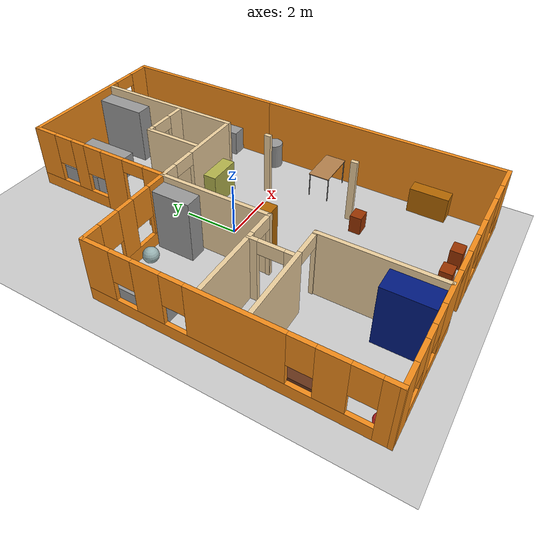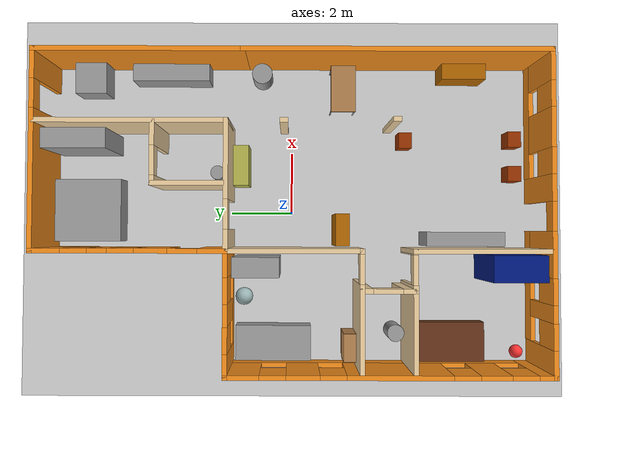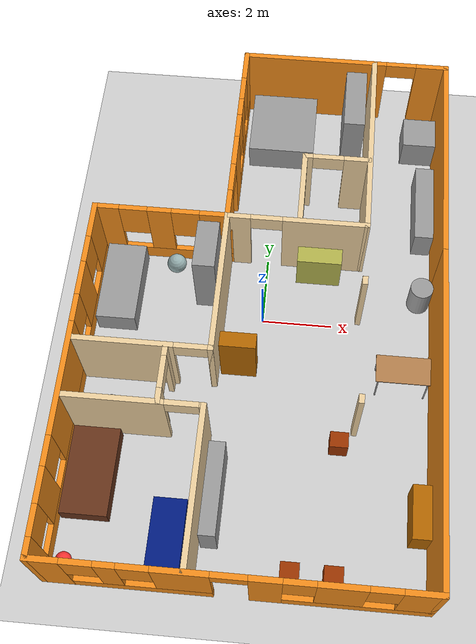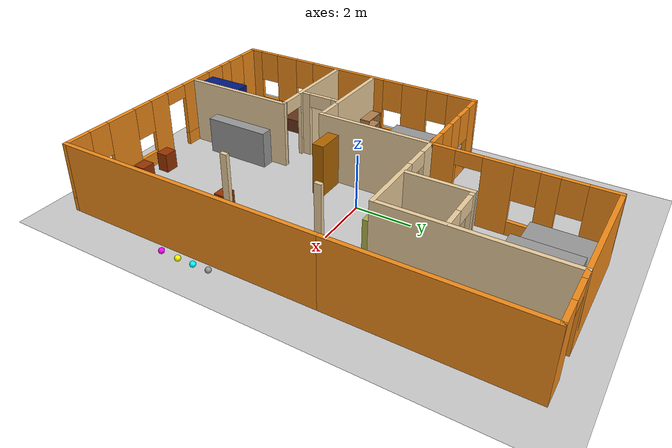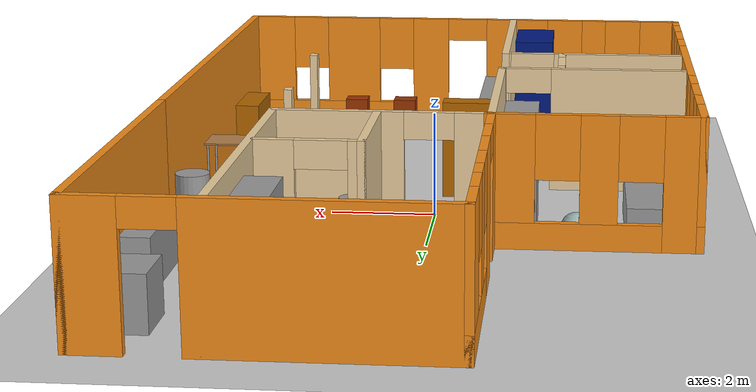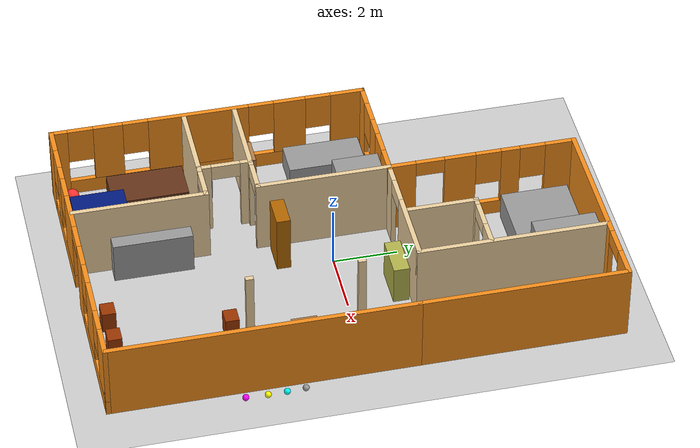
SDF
<sdf version="1.6">
 <world name="default">
  <light name="sun" type="directional">
   <pose>0 0 10 0 -0 0</pose>
   <diffuse>0.8 0.8 0.8 1</diffuse>
   <specular>0.2 0.2 0.2 1</specular>
   <attenuation>
    <range>1000</range>
    <constant>0.9</constant>
    <linear>0.01</linear>
    <quadratic>0.001</quadratic>
   </attenuation>
   <direction>-0.5 0.1 -0.9</direction>
  </light>
  <model name="ground_plane">
   <static>1</static>
   <link name="link">
    <collision name="collision">
     <geometry><plane><normal>0 0 1</normal><size>100 100</size></plane></geometry>
     <surface><friction><ode><mu>100</mu><mu2>50</mu2></ode></friction></surface>
    </collision>
    <visual name="visual">
     <cast_shadows>0</cast_shadows>
     <geometry><plane><normal>0 0 1</normal><size>100 100</size></plane></geometry>
     <material>
      <script><uri>file://media/materials/scripts/gazebo.material</uri><name>Gazebo/Grey</name></script>
     </material>
    </visual>
   </link>
  </model>
  <gravity>0 0 -9.8</gravity>
  <magnetic_field>6e-06 2.3e-05 -4.2e-05</magnetic_field>
  <atmosphere type="adiabatic"/>
  <physics name="default_physics" default="0" type="ode">
   <max_step_size>0.001</max_step_size>
   <real_time_factor>1</real_time_factor>
   <real_time_update_rate>1000</real_time_update_rate>
  </physics>
  <scene><ambient>0.4 0.4 0.4 1</ambient><background>0.7 0.7 0.7 1</background><shadows>1</shadows></scene>
  <spherical_coordinates>
   <surface_model>EARTH_WGS84</surface_model>
   <latitude_deg>0</latitude_deg>
   <longitude_deg>0</longitude_deg>
   <elevation>0</elevation>
   <heading_deg>0</heading_deg>
  </spherical_coordinates>
  <model name="house">
   <link name="Wall_103">
    <pose>-1.175 4.925 0 0 -0 1.5708</pose>
    <visual name="Wall_103_Visual_0">
     <pose>-2.54292 0 1.25 0 -0 0</pose>
     <geometry><box><size>0.914167 0.15 2.5</size></box></geometry>
     <material>
      <script><uri>file://media/materials/scripts/gazebo.material</uri><name>Gazebo/Orange</name></script>
      <ambient>1 1 1 1</ambient>
     </material>
     <meta><layer>0</layer></meta>
    </visual>
    <collision name="Wall_103_Collision_0">
     <geometry><box><size>0.914167 0.15 2.5</size></box></geometry>
     <pose>-2.54292 0 1.25 0 -0 0</pose>
    </collision>
    <visual name="Wall_103_Visual_1">
     <pose>-0.689609 0 1.25 0 -0 0</pose>
     <geometry><box><size>0.992449 0.15 2.5</size></box></geometry>
     <material>
      <script><uri>file://media/materials/scripts/gazebo.material</uri><name>Gazebo/Orange</name></script>
      <ambient>1 1 1 1</ambient>
     </material>
     <meta><layer>0</layer></meta>
    </visual>
    <collision name="Wall_103_Collision_1">
     <geometry><box><size>0.992449 0.15 2.5</size></box></geometry>
     <pose>-0.689609 0 1.25 0 -0 0</pose>
    </collision>
    <visual name="Wall_103_Visual_2">
     <pose>1.40331 0 0.25 0 -0 0</pose>
     <geometry><box><size>3.19338 0.15 0.5</size></box></geometry>
     <material>
      <script><uri>file://media/materials/scripts/gazebo.material</uri><name>Gazebo/Orange</name></script>
      <ambient>1 1 1 1</ambient>
     </material>
     <meta><layer>0</layer></meta>
    </visual>
    <collision name="Wall_103_Collision_2">
     <geometry><box><size>3.19338 0.15 0.5</size></box></geometry>
     <pose>1.40331 0 0.25 0 -0 0</pose>
    </collision>
    <visual name="Wall_103_Visual_3">
     <pose>0.905775 0 1.5 0 -0 0</pose>
     <geometry><box><size>0.598318 0.15 2</size></box></geometry>
     <material>
      <script><uri>file://media/materials/scripts/gazebo.material</uri><name>Gazebo/Orange</name></script>
      <ambient>1 1 1 1</ambient>
     </material>
     <meta><layer>0</layer></meta>
    </visual>
    <collision name="Wall_103_Collision_3">
     <geometry><box><size>0.598318 0.15 2</size></box></geometry>
     <pose>0.905775 0 1.5 0 -0 0</pose>
    </collision>
    <visual name="Wall_103_Visual_4">
     <pose>2.50247 0 1.5 0 -0 0</pose>
     <geometry><box><size>0.995066 0.15 2</size></box></geometry>
     <material>
      <script><uri>file://media/materials/scripts/gazebo.material</uri><name>Gazebo/Orange</name></script>
      <ambient>1 1 1 1</ambient>
     </material>
     <meta><layer>0</layer></meta>
    </visual>
    <collision name="Wall_103_Collision_4">
     <geometry><box><size>0.995066 0.15 2</size></box></geometry>
     <pose>2.50247 0 1.5 0 -0 0</pose>
    </collision>
    <visual name="Wall_103_Visual_5">
     <pose>0.206616 0 1.9 0 -0 0</pose>
     <geometry><box><size>0.8 0.15 1.2</size></box></geometry>
     <material>
      <script><uri>file://media/materials/scripts/gazebo.material</uri><name>Gazebo/Orange</name></script>
      <ambient>1 1 1 1</ambient>
     </material>
     <meta><layer>0</layer></meta>
    </visual>
    <collision name="Wall_103_Collision_5">
     <geometry><box><size>0.8 0.15 1.2</size></box></geometry>
     <pose>0.206616 0 1.9 0 -0 0</pose>
    </collision>
    <visual name="Wall_103_Visual_6">
     <pose>1.60493 0 1.9 0 -0 0</pose>
     <geometry><box><size>0.8 0.15 1.2</size></box></geometry>
     <material>
      <script><uri>file://media/materials/scripts/gazebo.material</uri><name>Gazebo/Orange</name></script>
      <ambient>1 1 1 1</ambient>
     </material>
     <meta><layer>0</layer></meta>
    </visual>
    <collision name="Wall_103_Collision_6">
     <geometry><box><size>0.8 0.15 1.2</size></box></geometry>
     <pose>1.60493 0 1.9 0 -0 0</pose>
    </collision>
    <visual name="Wall_103_Visual_7">
     <pose>-1.63583 0 2.25 0 -0 0</pose>
     <geometry><box><size>0.9 0.15 0.5</size></box></geometry>
     <material>
      <script><uri>file://media/materials/scripts/gazebo.material</uri><name>Gazebo/Orange</name></script>
      <ambient>1 1 1 1</ambient>
     </material>
     <meta><layer>0</layer></meta>
    </visual>
    <collision name="Wall_103_Collision_7">
     <geometry><box><size>0.9 0.15 0.5</size></box></geometry>
     <pose>-1.63583 0 2.25 0 -0 0</pose>
    </collision>
   </link>
   <link name="Wall_105">
    <pose>-3.02063 2 0 0 -0 0</pose>
    <visual name="Wall_105_Visual_0">
     <pose>-1.60034 0 1.25 0 -0 0</pose>
     <geometry><box><size>0.758079 0.15 2.5</size></box></geometry>
     <material>
      <script><uri>file://media/materials/scripts/gazebo.material</uri><name>Gazebo/Orange</name></script>
      <ambient>1 1 1 1</ambient>
     </material>
     <meta><layer>0</layer></meta>
    </visual>
    <collision name="Wall_105_Collision_0">
     <geometry><box><size>0.758079 0.15 2.5</size></box></geometry>
     <pose>-1.60034 0 1.25 0 -0 0</pose>
    </collision>
    <visual name="Wall_105_Visual_1">
     <pose>0.37904 0 0.25 0 -0 0</pose>
     <geometry><box><size>3.20067 0.15 0.5</size></box></geometry>
     <material>
      <script><uri>file://media/materials/scripts/gazebo.material</uri><name>Gazebo/Orange</name></script>
      <ambient>1 1 1 1</ambient>
     </material>
     <meta><layer>0</layer></meta>
    </visual>
    <collision name="Wall_105_Collision_1">
     <geometry><box><size>3.20067 0.15 0.5</size></box></geometry>
     <pose>0.37904 0 0.25 0 -0 0</pose>
    </collision>
    <visual name="Wall_105_Visual_2">
     <pose>-0.079355 0 1.5 0 -0 0</pose>
     <geometry><box><size>0.683879 0.15 2</size></box></geometry>
     <material>
      <script><uri>file://media/materials/scripts/gazebo.material</uri><name>Gazebo/Orange</name></script>
      <ambient>1 1 1 1</ambient>
     </material>
     <meta><layer>0</layer></meta>
    </visual>
    <collision name="Wall_105_Collision_2">
     <geometry><box><size>0.683879 0.15 2</size></box></geometry>
     <pose>-0.079355 0 1.5 0 -0 0</pose>
    </collision>
    <visual name="Wall_105_Visual_3">
     <pose>1.52098 0 1.5 0 -0 0</pose>
     <geometry><box><size>0.91679 0.15 2</size></box></geometry>
     <material>
      <script><uri>file://media/materials/scripts/gazebo.material</uri><name>Gazebo/Orange</name></script>
      <ambient>1 1 1 1</ambient>
     </material>
     <meta><layer>0</layer></meta>
    </visual>
    <collision name="Wall_105_Collision_3">
     <geometry><box><size>0.91679 0.15 2</size></box></geometry>
     <pose>1.52098 0 1.5 0 -0 0</pose>
    </collision>
    <visual name="Wall_105_Visual_4">
     <pose>-0.821295 0 1.9 0 -0 0</pose>
     <geometry><box><size>0.8 0.15 1.2</size></box></geometry>
     <material>
      <script><uri>file://media/materials/scripts/gazebo.material</uri><name>Gazebo/Orange</name></script>
      <ambient>1 1 1 1</ambient>
     </material>
     <meta><layer>0</layer></meta>
    </visual>
    <collision name="Wall_105_Collision_4">
     <geometry><box><size>0.8 0.15 1.2</size></box></geometry>
     <pose>-0.821295 0 1.9 0 -0 0</pose>
    </collision>
    <visual name="Wall_105_Visual_5">
     <pose>0.662584 0 1.9 0 -0 0</pose>
     <geometry><box><size>0.8 0.15 1.2</size></box></geometry>
     <material>
      <script><uri>file://media/materials/scripts/gazebo.material</uri><name>Gazebo/Orange</name></script>
      <ambient>1 1 1 1</ambient>
     </material>
     <meta><layer>0</layer></meta>
    </visual>
    <collision name="Wall_105_Collision_5">
     <geometry><box><size>0.8 0.15 1.2</size></box></geometry>
     <pose>0.662584 0 1.9 0 -0 0</pose>
    </collision>
   </link>
   <link name="Wall_107">
    <pose>1.875 7.85 0 0 -0 0</pose>
    <visual name="Wall_107_Visual_0">
     <pose>-0.942379 0 1.25 0 -0 0</pose>
     <geometry><box><size>4.36524 0.15 2.5</size></box></geometry>
     <material>
      <script><uri>file://media/materials/scripts/gazebo.material</uri><name>Gazebo/Orange</name></script>
      <ambient>1 1 1 1</ambient>
     </material>
     <meta><layer>0</layer></meta>
    </visual>
    <collision name="Wall_107_Collision_0">
     <geometry><box><size>4.36524 0.15 2.5</size></box></geometry>
     <pose>-0.942379 0 1.25 0 -0 0</pose>
    </collision>
    <visual name="Wall_107_Visual_1">
     <pose>2.63262 0 1.25 0 -0 0</pose>
     <geometry><box><size>0.984758 0.15 2.5</size></box></geometry>
     <material>
      <script><uri>file://media/materials/scripts/gazebo.material</uri><name>Gazebo/Orange</name></script>
      <ambient>1 1 1 1</ambient>
     </material>
     <meta><layer>0</layer></meta>
    </visual>
    <collision name="Wall_107_Collision_1">
     <geometry><box><size>0.984758 0.15 2.5</size></box></geometry>
     <pose>2.63262 0 1.25 0 -0 0</pose>
    </collision>
    <visual name="Wall_107_Visual_2">
     <pose>1.69024 0 2.25 0 -0 0</pose>
     <geometry><box><size>0.9 0.15 0.5</size></box></geometry>
     <material>
      <script><uri>file://media/materials/scripts/gazebo.material</uri><name>Gazebo/Orange</name></script>
      <ambient>1 1 1 1</ambient>
     </material>
     <meta><layer>0</layer></meta>
    </visual>
    <collision name="Wall_107_Collision_2">
     <geometry><box><size>0.9 0.15 0.5</size></box></geometry>
     <pose>1.69024 0 2.25 0 -0 0</pose>
    </collision>
   </link>
   <link name="Wall_116">
    <collision name="Wall_116_Collision">
     <geometry><box><size>6.5 0.15 2.5</size></box></geometry>
     <pose>0 0 1.25 0 -0 0</pose>
    </collision>
    <visual name="Wall_116_Visual">
     <pose>0 0 1.25 0 -0 0</pose>
     <geometry><box><size>6.5 0.15 2.5</size></box></geometry>
     <material>
      <script><uri>file://media/materials/scripts/gazebo.material</uri><name>Gazebo/Orange</name></script>
      <ambient>1 1 1 1</ambient>
     </material>
     <meta><layer>0</layer></meta>
    </visual>
    <pose>4.925 4.675 0 0 0 -1.5708</pose>
   </link>
   <link name="Wall_137">
    <collision name="Wall_137_Collision">
     <geometry><box><size>4.25 0.15 2.5</size></box></geometry>
     <pose>0 0 1.25 0 -0 0</pose>
    </collision>
    <visual name="Wall_137_Visual">
     <pose>0 0 1.25 0 -0 0</pose>
     <geometry><box><size>4.25 0.15 2.5</size></box></geometry>
     <material>
      <script><uri>file://media/materials/scripts/gazebo.material</uri><name>Gazebo/Grey</name></script>
      <ambient>0.921569 0.807843 0.615686 1</ambient>
     </material>
     <meta><layer>0</layer></meta>
    </visual>
    <pose>-1.175 -5.75 0 0 0 -1.5708</pose>
   </link>
   <link name="Wall_139">
    <pose>-2.975 -3.7 0 0 -0 3.14159</pose>
    <visual name="Wall_139_Visual_0">
     <pose>-1.78069 0 1.25 0 -0 0</pose>
     <geometry><box><size>0.188621 0.15 2.5</size></box></geometry>
     <material>
      <script><uri>file://media/materials/scripts/gazebo.material</uri><name>Gazebo/Grey</name></script>
      <ambient>0.921569 0.807843 0.615686 1</ambient>
     </material>
     <meta><layer>0</layer></meta>
    </visual>
    <collision name="Wall_139_Collision_0">
     <geometry><box><size>0.188621 0.15 2.5</size></box></geometry>
     <pose>-1.78069 0 1.25 0 -0 0</pose>
    </collision>
    <visual name="Wall_139_Visual_1">
     <pose>0.54431 0 1.25 0 -0 0</pose>
     <geometry><box><size>2.66138 0.15 2.5</size></box></geometry>
     <material>
      <script><uri>file://media/materials/scripts/gazebo.material</uri><name>Gazebo/Grey</name></script>
      <ambient>0.921569 0.807843 0.615686 1</ambient>
     </material>
     <meta><layer>0</layer></meta>
    </visual>
    <collision name="Wall_139_Collision_1">
     <geometry><box><size>2.66138 0.15 2.5</size></box></geometry>
     <pose>0.54431 0 1.25 0 -0 0</pose>
    </collision>
    <visual name="Wall_139_Visual_2">
     <pose>-1.23638 0 2.25 0 -0 0</pose>
     <geometry><box><size>0.9 0.15 0.5</size></box></geometry>
     <material>
      <script><uri>file://media/materials/scripts/gazebo.material</uri><name>Gazebo/Grey</name></script>
      <ambient>0.921569 0.807843 0.615686 1</ambient>
     </material>
     <meta><layer>0</layer></meta>
    </visual>
    <collision name="Wall_139_Collision_2">
     <geometry><box><size>0.9 0.15 0.5</size></box></geometry>
     <pose>-1.23638 0 2.25 0 -0 0</pose>
    </collision>
   </link>
   <link name="Wall_143">
    <pose>-2.36246 -2.90327 0 0 0 -1.5708</pose>
    <visual name="Wall_143_Visual_0">
     <pose>-0.667997 0 1.25 0 -0 0</pose>
     <geometry><box><size>0.373609 0.15 2.5</size></box></geometry>
     <material>
      <script><uri>file://media/materials/scripts/gazebo.material</uri><name>Gazebo/Grey</name></script>
      <ambient>0.921569 0.807843 0.615686 1</ambient>
     </material>
     <meta><layer>0</layer></meta>
    </visual>
    <collision name="Wall_143_Collision_0">
     <geometry><box><size>0.373609 0.15 2.5</size></box></geometry>
     <pose>-0.667997 0 1.25 0 -0 0</pose>
    </collision>
    <visual name="Wall_143_Visual_1">
     <pose>0.636805 0 1.25 0 -0 0</pose>
     <geometry><box><size>0.435994 0.15 2.5</size></box></geometry>
     <material>
      <script><uri>file://media/materials/scripts/gazebo.material</uri><name>Gazebo/Grey</name></script>
      <ambient>0.921569 0.807843 0.615686 1</ambient>
     </material>
     <meta><layer>0</layer></meta>
    </visual>
    <collision name="Wall_143_Collision_1">
     <geometry><box><size>0.435994 0.15 2.5</size></box></geometry>
     <pose>0.636805 0 1.25 0 -0 0</pose>
    </collision>
    <visual name="Wall_143_Visual_2">
     <pose>-0.031192 0 2.25 0 -0 0</pose>
     <geometry><box><size>0.9 0.15 0.5</size></box></geometry>
     <material>
      <script><uri>file://media/materials/scripts/gazebo.material</uri><name>Gazebo/Grey</name></script>
      <ambient>0.921569 0.807843 0.615686 1</ambient>
     </material>
     <meta><layer>0</layer></meta>
    </visual>
    <collision name="Wall_143_Collision_2">
     <geometry><box><size>0.9 0.15 0.5</size></box></geometry>
     <pose>-0.031192 0 2.25 0 -0 0</pose>
    </collision>
   </link>
   <link name="Wall_149">
    <pose>0.829374 2 0 0 -0 0</pose>
    <visual name="Wall_149_Visual_0">
     <pose>-1.67334 0 1.25 0 -0 0</pose>
     <geometry><box><size>0.653328 0.15 2.5</size></box></geometry>
     <material>
      <script><uri>file://media/materials/scripts/gazebo.material</uri><name>Gazebo/Grey</name></script>
      <ambient>0.921569 0.807843 0.615686 1</ambient>
     </material>
     <meta><layer>0</layer></meta>
    </visual>
    <collision name="Wall_149_Collision_0">
     <geometry><box><size>0.653328 0.15 2.5</size></box></geometry>
     <pose>-1.67334 0 1.25 0 -0 0</pose>
    </collision>
    <visual name="Wall_149_Visual_1">
     <pose>0.776664 0 1.25 0 -0 0</pose>
     <geometry><box><size>2.44667 0.15 2.5</size></box></geometry>
     <material>
      <script><uri>file://media/materials/scripts/gazebo.material</uri><name>Gazebo/Grey</name></script>
      <ambient>0.921569 0.807843 0.615686 1</ambient>
     </material>
     <meta><layer>0</layer></meta>
    </visual>
    <collision name="Wall_149_Collision_1">
     <geometry><box><size>2.44667 0.15 2.5</size></box></geometry>
     <pose>0.776664 0 1.25 0 -0 0</pose>
    </collision>
    <visual name="Wall_149_Visual_2">
     <pose>-0.896672 0 2.25 0 -0 0</pose>
     <geometry><box><size>0.9 0.15 0.5</size></box></geometry>
     <material>
      <script><uri>file://media/materials/scripts/gazebo.material</uri><name>Gazebo/Grey</name></script>
      <ambient>0.921569 0.807843 0.615686 1</ambient>
     </material>
     <meta><layer>0</layer></meta>
    </visual>
    <collision name="Wall_149_Collision_2">
     <geometry><box><size>0.9 0.15 0.5</size></box></geometry>
     <pose>-0.896672 0 2.25 0 -0 0</pose>
    </collision>
   </link>
   <link name="Wall_151">
    <collision name="Wall_151_Collision">
     <geometry><box><size>6 0.15 2.5</size></box></geometry>
     <pose>0 0 1.25 0 -0 0</pose>
    </collision>
    <visual name="Wall_151_Visual">
     <pose>0 0 1.25 0 -0 0</pose>
     <geometry><box><size>6 0.15 2.5</size></box></geometry>
     <material>
      <script><uri>file://media/materials/scripts/gazebo.material</uri><name>Gazebo/Grey</name></script>
      <ambient>0.921569 0.807843 0.615686 1</ambient>
     </material>
     <meta><layer>0</layer></meta>
    </visual>
    <pose>2.75437 4.925 0 0 -0 1.5708</pose>
   </link>
   <link name="Wall_153">
    <collision name="Wall_153_Collision">
     <geometry><box><size>2.25 0.15 2.5</size></box></geometry>
     <pose>0 0 1.25 0 -0 0</pose>
    </collision>
    <visual name="Wall_153_Visual">
     <pose>0 0 1.25 0 -0 0</pose>
     <geometry><box><size>2.25 0.15 2.5</size></box></geometry>
     <material>
      <script><uri>file://media/materials/scripts/gazebo.material</uri><name>Gazebo/Grey</name></script>
      <ambient>0.921569 0.807843 0.615686 1</ambient>
     </material>
     <meta><layer>0</layer></meta>
    </visual>
    <pose>0.863268 3.17275 0 0 -0 1.5708</pose>
   </link>
   <link name="Wall_154">
    <pose>1.78827 4.22275 0 0 -0 0</pose>
    <visual name="Wall_154_Visual_0">
     <pose>-0.847175 0 1.25 0 -0 0</pose>
     <geometry><box><size>0.30565 0.15 2.5</size></box></geometry>
     <material>
      <script><uri>file://media/materials/scripts/gazebo.material</uri><name>Gazebo/Grey</name></script>
      <ambient>0.921569 0.807843 0.615686 1</ambient>
     </material>
     <meta><layer>0</layer></meta>
    </visual>
    <collision name="Wall_154_Collision_0">
     <geometry><box><size>0.30565 0.15 2.5</size></box></geometry>
     <pose>-0.847175 0 1.25 0 -0 0</pose>
    </collision>
    <visual name="Wall_154_Visual_1">
     <pose>0.602825 0 1.25 0 -0 0</pose>
     <geometry><box><size>0.79435 0.15 2.5</size></box></geometry>
     <material>
      <script><uri>file://media/materials/scripts/gazebo.material</uri><name>Gazebo/Grey</name></script>
      <ambient>0.921569 0.807843 0.615686 1</ambient>
     </material>
     <meta><layer>0</layer></meta>
    </visual>
    <collision name="Wall_154_Collision_1">
     <geometry><box><size>0.79435 0.15 2.5</size></box></geometry>
     <pose>0.602825 0 1.25 0 -0 0</pose>
    </collision>
    <visual name="Wall_154_Visual_2">
     <pose>-0.24435 0 2.25 0 -0 0</pose>
     <geometry><box><size>0.9 0.15 0.5</size></box></geometry>
     <material>
      <script><uri>file://media/materials/scripts/gazebo.material</uri><name>Gazebo/Grey</name></script>
      <ambient>0.921569 0.807843 0.615686 1</ambient>
     </material>
     <meta><layer>0</layer></meta>
    </visual>
    <collision name="Wall_154_Collision_2">
     <geometry><box><size>0.9 0.15 0.5</size></box></geometry>
     <pose>-0.24435 0 2.25 0 -0 0</pose>
    </collision>
   </link>
   <link name="Wall_156">
    <collision name="Wall_156_Collision">
     <geometry><box><size>0.25 0.15 2.5</size></box></geometry>
     <pose>0 0 1.25 0 -0 0</pose>
    </collision>
    <visual name="Wall_156_Visual">
     <pose>0 0 1.25 0 -0 0</pose>
     <geometry><box><size>0.25 0.15 2.5</size></box></geometry>
     <material>
      <script><uri>file://media/materials/scripts/gazebo.material</uri><name>Gazebo/Grey</name></script>
      <ambient>0.921569 0.807843 0.615686 1</ambient>
     </material>
     <meta><layer>0</layer></meta>
    </visual>
    <pose>2.76084 0.255188 0 0 0 -1.5708</pose>
   </link>
   <link name="Wall_158">
    <collision name="Wall_158_Collision">
     <geometry><box><size>0.25 0.15 2.5</size></box></geometry>
     <pose>0 0 1.25 0 -0 0</pose>
    </collision>
    <visual name="Wall_158_Visual">
     <pose>0 0 1.25 0 -0 0</pose>
     <geometry><box><size>0.25 0.15 2.5</size></box></geometry>
     <material>
      <script><uri>file://media/materials/scripts/gazebo.material</uri><name>Gazebo/Grey</name></script>
      <ambient>0.921569 0.807843 0.615686 1</ambient>
     </material>
     <meta><layer>0</layer></meta>
    </visual>
    <pose>2.80209 -3.16869 0 0 0 -1.5708</pose>
   </link>
   <link name="Wall_62">
    <pose>0 -7.85 0 0 -0 0</pose>
    <visual name="Wall_62_Visual_0">
     <pose>-4.55783 0 1.25 0 -0 0</pose>
     <geometry><box><size>0.88435 0.15 2.5</size></box></geometry>
     <material>
      <script><uri>file://media/materials/scripts/gazebo.material</uri><name>Gazebo/Orange</name></script>
      <ambient>1 1 1 1</ambient>
     </material>
     <meta><layer>0</layer></meta>
    </visual>
    <collision name="Wall_62_Collision_0">
     <geometry><box><size>0.88435 0.15 2.5</size></box></geometry>
     <pose>-4.55783 0 1.25 0 -0 0</pose>
    </collision>
    <visual name="Wall_62_Visual_1">
     <pose>0.7542 0 1.25 0 -0 0</pose>
     <geometry><box><size>0.820686 0.15 2.5</size></box></geometry>
     <material>
      <script><uri>file://media/materials/scripts/gazebo.material</uri><name>Gazebo/Orange</name></script>
      <ambient>1 1 1 1</ambient>
     </material>
     <meta><layer>0</layer></meta>
    </visual>
    <collision name="Wall_62_Collision_1">
     <geometry><box><size>0.820686 0.15 2.5</size></box></geometry>
     <pose>0.7542 0 1.25 0 -0 0</pose>
    </collision>
    <visual name="Wall_62_Visual_2">
     <pose>-2.3359 0 0.25 0 -0 0</pose>
     <geometry><box><size>3.55951 0.15 0.5</size></box></geometry>
     <material>
      <script><uri>file://media/materials/scripts/gazebo.material</uri><name>Gazebo/Orange</name></script>
      <ambient>1 1 1 1</ambient>
     </material>
     <meta><layer>0</layer></meta>
    </visual>
    <collision name="Wall_62_Collision_2">
     <geometry><box><size>3.55951 0.15 0.5</size></box></geometry>
     <pose>-2.3359 0 0.25 0 -0 0</pose>
    </collision>
    <visual name="Wall_62_Visual_3">
     <pose>3.08227 0 0.25 0 -0 0</pose>
     <geometry><box><size>3.83546 0.15 0.5</size></box></geometry>
     <material>
      <script><uri>file://media/materials/scripts/gazebo.material</uri><name>Gazebo/Orange</name></script>
      <ambient>1 1 1 1</ambient>
     </material>
     <meta><layer>0</layer></meta>
    </visual>
    <collision name="Wall_62_Collision_3">
     <geometry><box><size>3.83546 0.15 0.5</size></box></geometry>
     <pose>3.08227 0 0.25 0 -0 0</pose>
    </collision>
    <visual name="Wall_62_Visual_4">
     <pose>-3.04531 0 1.5 0 -0 0</pose>
     <geometry><box><size>0.540674 0.15 2</size></box></geometry>
     <material>
      <script><uri>file://media/materials/scripts/gazebo.material</uri><name>Gazebo/Orange</name></script>
      <ambient>1 1 1 1</ambient>
     </material>
     <meta><layer>0</layer></meta>
    </visual>
    <collision name="Wall_62_Collision_4">
     <geometry><box><size>0.540674 0.15 2</size></box></geometry>
     <pose>-3.04531 0 1.5 0 -0 0</pose>
    </collision>
    <visual name="Wall_62_Visual_5">
     <pose>-1.26556 0 1.5 0 -0 0</pose>
     <geometry><box><size>1.41883 0.15 2</size></box></geometry>
     <material>
      <script><uri>file://media/materials/scripts/gazebo.material</uri><name>Gazebo/Orange</name></script>
      <ambient>1 1 1 1</ambient>
     </material>
     <meta><layer>0</layer></meta>
    </visual>
    <collision name="Wall_62_Collision_5">
     <geometry><box><size>1.41883 0.15 2</size></box></geometry>
     <pose>-1.26556 0 1.5 0 -0 0</pose>
    </collision>
    <visual name="Wall_62_Visual_6">
     <pose>-1.26556 0 1.5 0 -0 0</pose>
     <geometry><box><size>1.41883 0.15 2</size></box></geometry>
     <material>
      <script><uri>file://media/materials/scripts/gazebo.material</uri><name>Gazebo/Orange</name></script>
      <ambient>1 1 1 1</ambient>
     </material>
     <meta><layer>0</layer></meta>
    </visual>
    <collision name="Wall_62_Collision_6">
     <geometry><box><size>1.41883 0.15 2</size></box></geometry>
     <pose>-1.26556 0 1.5 0 -0 0</pose>
    </collision>
    <visual name="Wall_62_Visual_7">
     <pose>2.57521 0 1.5 0 -0 0</pose>
     <geometry><box><size>1.22132 0.15 2</size></box></geometry>
     <material>
      <script><uri>file://media/materials/scripts/gazebo.material</uri><name>Gazebo/Orange</name></script>
      <ambient>1 1 1 1</ambient>
     </material>
     <meta><layer>0</layer></meta>
    </visual>
    <collision name="Wall_62_Collision_7">
     <geometry><box><size>1.22132 0.15 2</size></box></geometry>
     <pose>2.57521 0 1.5 0 -0 0</pose>
    </collision>
    <visual name="Wall_62_Visual_8">
     <pose>4.49293 0 1.5 0 -0 0</pose>
     <geometry><box><size>1.01413 0.15 2</size></box></geometry>
     <material>
      <script><uri>file://media/materials/scripts/gazebo.material</uri><name>Gazebo/Orange</name></script>
      <ambient>1 1 1 1</ambient>
     </material>
     <meta><layer>0</layer></meta>
    </visual>
    <collision name="Wall_62_Collision_8">
     <geometry><box><size>1.01413 0.15 2</size></box></geometry>
     <pose>4.49293 0 1.5 0 -0 0</pose>
    </collision>
    <visual name="Wall_62_Visual_9">
     <pose>-3.71565 0 1.9 0 -0 0</pose>
     <geometry><box><size>0.8 0.15 1.2</size></box></geometry>
     <material>
      <script><uri>file://media/materials/scripts/gazebo.material</uri><name>Gazebo/Orange</name></script>
      <ambient>1 1 1 1</ambient>
     </material>
     <meta><layer>0</layer></meta>
    </visual>
    <collision name="Wall_62_Collision_9">
     <geometry><box><size>0.8 0.15 1.2</size></box></geometry>
     <pose>-3.71565 0 1.9 0 -0 0</pose>
    </collision>
    <visual name="Wall_62_Visual_10">
     <pose>1.56454 0 1.9 0 -0 0</pose>
     <geometry><box><size>0.8 0.15 1.2</size></box></geometry>
     <material>
      <script><uri>file://media/materials/scripts/gazebo.material</uri><name>Gazebo/Orange</name></script>
      <ambient>1 1 1 1</ambient>
     </material>
     <meta><layer>0</layer></meta>
    </visual>
    <collision name="Wall_62_Collision_10">
     <geometry><box><size>0.8 0.15 1.2</size></box></geometry>
     <pose>1.56454 0 1.9 0 -0 0</pose>
    </collision>
    <visual name="Wall_62_Visual_11">
     <pose>-2.37498 0 1.9 0 -0 0</pose>
     <geometry><box><size>0.8 0.15 1.2</size></box></geometry>
     <material>
      <script><uri>file://media/materials/scripts/gazebo.material</uri><name>Gazebo/Orange</name></script>
      <ambient>1 1 1 1</ambient>
     </material>
     <meta><layer>0</layer></meta>
    </visual>
    <collision name="Wall_62_Collision_11">
     <geometry><box><size>0.8 0.15 1.2</size></box></geometry>
     <pose>-2.37498 0 1.9 0 -0 0</pose>
    </collision>
    <visual name="Wall_62_Visual_12">
     <pose>3.58587 0 1.9 0 -0 0</pose>
     <geometry><box><size>0.8 0.15 1.2</size></box></geometry>
     <material>
      <script><uri>file://media/materials/scripts/gazebo.material</uri><name>Gazebo/Orange</name></script>
      <ambient>1 1 1 1</ambient>
     </material>
     <meta><layer>0</layer></meta>
    </visual>
    <collision name="Wall_62_Collision_12">
     <geometry><box><size>0.8 0.15 1.2</size></box></geometry>
     <pose>3.58587 0 1.9 0 -0 0</pose>
    </collision>
    <visual name="Wall_62_Visual_13">
     <pose>-0.106143 0 2.25 0 -0 0</pose>
     <geometry><box><size>0.9 0.15 0.5</size></box></geometry>
     <material>
      <script><uri>file://media/materials/scripts/gazebo.material</uri><name>Gazebo/Orange</name></script>
      <ambient>1 1 1 1</ambient>
     </material>
     <meta><layer>0</layer></meta>
    </visual>
    <collision name="Wall_62_Collision_13">
     <geometry><box><size>0.9 0.15 0.5</size></box></geometry>
     <pose>-0.106143 0 2.25 0 -0 0</pose>
    </collision>
    <visual name="Wall_62_Visual_14">
     <pose>-0.106143 0 2.25 0 -0 0</pose>
     <geometry><box><size>0.9 0.15 0.5</size></box></geometry>
     <material>
      <script><uri>file://media/materials/scripts/gazebo.material</uri><name>Gazebo/Orange</name></script>
      <ambient>1 1 1 1</ambient>
     </material>
     <meta><layer>0</layer></meta>
    </visual>
    <collision name="Wall_62_Collision_14">
     <geometry><box><size>0.9 0.15 0.5</size></box></geometry>
     <pose>-0.106143 0 2.25 0 -0 0</pose>
    </collision>
   </link>
   <link name="Wall_64">
    <pose>-4.925 -2.925 0 0 -0 1.5708</pose>
    <visual name="Wall_64_Visual_0">
     <pose>-4.71504 0 1.25 0 -0 0</pose>
     <geometry><box><size>0.569922 0.15 2.5</size></box></geometry>
     <material>
      <script><uri>file://media/materials/scripts/gazebo.material</uri><name>Gazebo/Orange</name></script>
      <ambient>1 1 1 1</ambient>
     </material>
     <meta><layer>0</layer></meta>
    </visual>
    <collision name="Wall_64_Collision_0">
     <geometry><box><size>0.569922 0.15 2.5</size></box></geometry>
     <pose>-4.71504 0 1.25 0 -0 0</pose>
    </collision>
    <visual name="Wall_64_Visual_1">
     <pose>0.284961 0 0.25 0 -0 0</pose>
     <geometry><box><size>9.43008 0.15 0.5</size></box></geometry>
     <material>
      <script><uri>file://media/materials/scripts/gazebo.material</uri><name>Gazebo/Orange</name></script>
      <ambient>1 1 1 1</ambient>
     </material>
     <meta><layer>0</layer></meta>
    </visual>
    <collision name="Wall_64_Collision_1">
     <geometry><box><size>9.43008 0.15 0.5</size></box></geometry>
     <pose>0.284961 0 0.25 0 -0 0</pose>
    </collision>
    <visual name="Wall_64_Visual_2">
     <pose>-3.1638 0 1.5 0 -0 0</pose>
     <geometry><box><size>0.932564 0.15 2</size></box></geometry>
     <material>
      <script><uri>file://media/materials/scripts/gazebo.material</uri><name>Gazebo/Orange</name></script>
      <ambient>1 1 1 1</ambient>
     </material>
     <meta><layer>0</layer></meta>
    </visual>
    <collision name="Wall_64_Collision_2">
     <geometry><box><size>0.932564 0.15 2</size></box></geometry>
     <pose>-3.1638 0 1.5 0 -0 0</pose>
    </collision>
    <visual name="Wall_64_Visual_3">
     <pose>-0.307129 0 1.5 0 -0 0</pose>
     <geometry><box><size>3.18077 0.15 2</size></box></geometry>
     <material>
      <script><uri>file://media/materials/scripts/gazebo.material</uri><name>Gazebo/Orange</name></script>
      <ambient>1 1 1 1</ambient>
     </material>
     <meta><layer>0</layer></meta>
    </visual>
    <collision name="Wall_64_Collision_3">
     <geometry><box><size>3.18077 0.15 2</size></box></geometry>
     <pose>-0.307129 0 1.5 0 -0 0</pose>
    </collision>
    <visual name="Wall_64_Visual_4">
     <pose>2.59079 0 1.5 0 -0 0</pose>
     <geometry><box><size>1.01507 0.15 2</size></box></geometry>
     <material>
      <script><uri>file://media/materials/scripts/gazebo.material</uri><name>Gazebo/Orange</name></script>
      <ambient>1 1 1 1</ambient>
     </material>
     <meta><layer>0</layer></meta>
    </visual>
    <collision name="Wall_64_Collision_4">
     <geometry><box><size>1.01507 0.15 2</size></box></geometry>
     <pose>2.59079 0 1.5 0 -0 0</pose>
    </collision>
    <visual name="Wall_64_Visual_5">
     <pose>4.44916 0 1.5 0 -0 0</pose>
     <geometry><box><size>1.10168 0.15 2</size></box></geometry>
     <material>
      <script><uri>file://media/materials/scripts/gazebo.material</uri><name>Gazebo/Orange</name></script>
      <ambient>1 1 1 1</ambient>
     </material>
     <meta><layer>0</layer></meta>
    </visual>
    <collision name="Wall_64_Collision_5">
     <geometry><box><size>1.10168 0.15 2</size></box></geometry>
     <pose>4.44916 0 1.5 0 -0 0</pose>
    </collision>
    <visual name="Wall_64_Visual_6">
     <pose>-4.03008 0 1.9 0 -0 0</pose>
     <geometry><box><size>0.8 0.15 1.2</size></box></geometry>
     <material>
      <script><uri>file://media/materials/scripts/gazebo.material</uri><name>Gazebo/Orange</name></script>
      <ambient>1 1 1 1</ambient>
     </material>
     <meta><layer>0</layer></meta>
    </visual>
    <collision name="Wall_64_Collision_6">
     <geometry><box><size>0.8 0.15 1.2</size></box></geometry>
     <pose>-4.03008 0 1.9 0 -0 0</pose>
    </collision>
    <visual name="Wall_64_Visual_7">
     <pose>-2.29751 0 1.9 0 -0 0</pose>
     <geometry><box><size>0.8 0.15 1.2</size></box></geometry>
     <material>
      <script><uri>file://media/materials/scripts/gazebo.material</uri><name>Gazebo/Orange</name></script>
      <ambient>1 1 1 1</ambient>
     </material>
     <meta><layer>0</layer></meta>
    </visual>
    <collision name="Wall_64_Collision_7">
     <geometry><box><size>0.8 0.15 1.2</size></box></geometry>
     <pose>-2.29751 0 1.9 0 -0 0</pose>
    </collision>
    <visual name="Wall_64_Visual_8">
     <pose>1.68326 0 1.9 0 -0 0</pose>
     <geometry><box><size>0.8 0.15 1.2</size></box></geometry>
     <material>
      <script><uri>file://media/materials/scripts/gazebo.material</uri><name>Gazebo/Orange</name></script>
      <ambient>1 1 1 1</ambient>
     </material>
     <meta><layer>0</layer></meta>
    </visual>
    <collision name="Wall_64_Collision_8">
     <geometry><box><size>0.8 0.15 1.2</size></box></geometry>
     <pose>1.68326 0 1.9 0 -0 0</pose>
    </collision>
    <visual name="Wall_64_Visual_9">
     <pose>3.49832 0 1.9 0 -0 0</pose>
     <geometry><box><size>0.8 0.15 1.2</size></box></geometry>
     <material>
      <script><uri>file://media/materials/scripts/gazebo.material</uri><name>Gazebo/Orange</name></script>
      <ambient>1 1 1 1</ambient>
     </material>
     <meta><layer>0</layer></meta>
    </visual>
    <collision name="Wall_64_Collision_9">
     <geometry><box><size>0.8 0.15 1.2</size></box></geometry>
     <pose>3.49832 0 1.9 0 -0 0</pose>
    </collision>
   </link>
   <link name="Wall_66">
    <collision name="Wall_66_Collision">
     <geometry><box><size>9.5 0.15 2.5</size></box></geometry>
     <pose>0 0 1.25 0 -0 0</pose>
    </collision>
    <visual name="Wall_66_Visual">
     <pose>0 0 1.25 0 -0 0</pose>
     <geometry><box><size>9.5 0.15 2.5</size></box></geometry>
     <material>
      <script><uri>file://media/materials/scripts/gazebo.material</uri><name>Gazebo/Orange</name></script>
      <ambient>1 1 1 1</ambient>
     </material>
     <meta><layer>0</layer></meta>
    </visual>
    <pose>4.925 -3.175 0 0 0 -1.5708</pose>
   </link>
   <link name="Wall_91">
    <pose>-2.975 -2.1 0 0 -0 0</pose>
    <visual name="Wall_91_Visual_0">
     <pose>-0.53002 0 1.25 0 -0 0</pose>
     <geometry><box><size>2.68996 0.15 2.5</size></box></geometry>
     <material>
      <script><uri>file://media/materials/scripts/gazebo.material</uri><name>Gazebo/Grey</name></script>
      <ambient>0.921569 0.807843 0.615686 1</ambient>
     </material>
     <meta><layer>0</layer></meta>
    </visual>
    <collision name="Wall_91_Collision_0">
     <geometry><box><size>2.68996 0.15 2.5</size></box></geometry>
     <pose>-0.53002 0 1.25 0 -0 0</pose>
    </collision>
    <visual name="Wall_91_Visual_1">
     <pose>1.79498 0 1.25 0 -0 0</pose>
     <geometry><box><size>0.16004 0.15 2.5</size></box></geometry>
     <material>
      <script><uri>file://media/materials/scripts/gazebo.material</uri><name>Gazebo/Grey</name></script>
      <ambient>0.921569 0.807843 0.615686 1</ambient>
     </material>
     <meta><layer>0</layer></meta>
    </visual>
    <collision name="Wall_91_Collision_1">
     <geometry><box><size>0.16004 0.15 2.5</size></box></geometry>
     <pose>1.79498 0 1.25 0 -0 0</pose>
    </collision>
    <visual name="Wall_91_Visual_2">
     <pose>1.26496 0 2.25 0 -0 0</pose>
     <geometry><box><size>0.9 0.15 0.5</size></box></geometry>
     <material>
      <script><uri>file://media/materials/scripts/gazebo.material</uri><name>Gazebo/Grey</name></script>
      <ambient>0.921569 0.807843 0.615686 1</ambient>
     </material>
     <meta><layer>0</layer></meta>
    </visual>
    <collision name="Wall_91_Collision_2">
     <geometry><box><size>0.9 0.15 0.5</size></box></geometry>
     <pose>1.26496 0 2.25 0 -0 0</pose>
    </collision>
   </link>
   <link name="Wall_92">
    <collision name="Wall_92_Collision">
     <geometry><box><size>4.25 0.15 2.5</size></box></geometry>
     <pose>0 0 1.25 0 -0 0</pose>
    </collision>
    <visual name="Wall_92_Visual">
     <pose>0 0 1.25 0 -0 0</pose>
     <geometry><box><size>4.25 0.15 2.5</size></box></geometry>
     <material>
      <script><uri>file://media/materials/scripts/gazebo.material</uri><name>Gazebo/Grey</name></script>
      <ambient>0.921569 0.807843 0.615686 1</ambient>
     </material>
     <meta><layer>0</layer></meta>
    </visual>
    <pose>-1.175 -0.05 0 0 -0 1.5708</pose>
   </link>
   <static>1</static>
  </model>
  <model name="bookshelf_0">
   <static>1</static>
   <link name="link">
    <inertial><mass>1</mass></inertial>
    <collision name="back">
     <pose>0 0.005 0.6 0 -0 0</pose>
     <geometry><box><size>0.9 0.01 1.2</size></box></geometry>
    </collision>
    <visual name="visual1">
     <pose>0 0.005 0.6 0 -0 0</pose>
     <geometry><box><size>0.9 0.01 1.2</size></box></geometry>
     <material>
      <script><uri>file://media/materials/scripts/gazebo.material</uri><name>Gazebo/Wood</name></script>
     </material>
    </visual>
    <collision name="left_side">
     <pose>0.45 -0.195 0.6 0 -0 0</pose>
     <geometry><box><size>0.02 0.4 1.2</size></box></geometry>
    </collision>
    <visual name="visual2">
     <pose>0.45 -0.195 0.6 0 -0 0</pose>
     <geometry><box><size>0.02 0.4 1.2</size></box></geometry>
     <material>
      <script><uri>file://media/materials/scripts/gazebo.material</uri><name>Gazebo/Wood</name></script>
     </material>
    </visual>
    <collision name="right_side">
     <pose>-0.45 -0.195 0.6 0 -0 0</pose>
     <geometry><box><size>0.02 0.4 1.2</size></box></geometry>
    </collision>
    <visual name="visual3">
     <pose>-0.45 -0.195 0.6 0 -0 0</pose>
     <geometry><box><size>0.02 0.4 1.2</size></box></geometry>
     <material>
      <script><uri>file://media/materials/scripts/gazebo.material</uri><name>Gazebo/Wood</name></script>
     </material>
    </visual>
    <collision name="bottom">
     <pose>0 -0.195 0.03 0 -0 0</pose>
     <geometry><box><size>0.88 0.4 0.06</size></box></geometry>
    </collision>
    <visual name="visual4">
     <pose>0 -0.195 0.03 0 -0 0</pose>
     <geometry><box><size>0.88 0.4 0.06</size></box></geometry>
     <material>
      <script><uri>file://media/materials/scripts/gazebo.material</uri><name>Gazebo/Wood</name></script>
     </material>
    </visual>
    <collision name="top">
     <pose>0 -0.195 1.19 0 -0 0</pose>
     <geometry><box><size>0.88 0.4 0.02</size></box></geometry>
    </collision>
    <visual name="visual5">
     <pose>0 -0.195 1.19 0 -0 0</pose>
     <geometry><box><size>0.88 0.4 0.02</size></box></geometry>
     <material>
      <script><uri>file://media/materials/scripts/gazebo.material</uri><name>Gazebo/Wood</name></script>
     </material>
    </visual>
    <collision name="low_shelf">
     <pose>0 -0.195 0.43 0 -0 0</pose>
     <geometry><box><size>0.88 0.4 0.02</size></box></geometry>
    </collision>
    <visual name="visual6">
     <pose>0 -0.195 0.43 0 -0 0</pose>
     <geometry><box><size>0.88 0.4 0.02</size></box></geometry>
     <material>
      <script><uri>file://media/materials/scripts/gazebo.material</uri><name>Gazebo/Wood</name></script>
     </material>
    </visual>
    <collision name="high_shelf">
     <pose>0 -0.195 0.8 0 -0 0</pose>
     <geometry><box><size>0.88 0.4 0.02</size></box></geometry>
    </collision>
    <visual name="visual7">
     <pose>0 -0.195 0.8 0 -0 0</pose>
     <geometry><box><size>0.88 0.4 0.02</size></box></geometry>
     <material>
      <script><uri>file://media/materials/scripts/gazebo.material</uri><name>Gazebo/Wood</name></script>
     </material>
    </visual>
   </link>
   <pose>-4.25914 -2.02776 0 0 0 -3.14</pose>
  </model>
  <model name="my_ball4">
   <link name="link_0">
    <inertial>
     <mass>1</mass>
     <inertia><ixx>0.1</ixx><ixy>0</ixy><ixz>0</ixz><iyy>0.1</iyy><iyz>0</iyz><izz>0.1</izz></inertia>
    </inertial>
    <visual name="visual">
     <geometry><sphere><radius>0.1</radius></sphere></geometry>
     <material>
      <lighting>1</lighting>
      <script><uri>file://media/materials/scripts/gazebo.material</uri><name>Gazebo/Grey</name></script>
      <shader type="pixel"><normal_map>__default__</normal_map></shader>
      <ambient>1 1 0 1</ambient>
      <diffuse>1 1 0 1</diffuse>
      <specular>1 1 0 1</specular>
      <emissive>1 1 0 1</emissive>
     </material>
    </visual>
    <collision name="collision">
     <geometry><sphere><radius>0.1</radius></sphere></geometry>
     <surface>
      <friction>
       <ode><mu>1</mu><mu2>1</mu2><fdir1>0 0 0</fdir1><slip1>0</slip1><slip2>0</slip2></ode>
       <torsional>
        <coefficient>1</coefficient>
        <patch_radius>0</patch_radius>
        <surface_radius>0</surface_radius>
        <use_patch_radius>1</use_patch_radius>
        <ode><slip>0</slip></ode>
       </torsional>
      </friction>
      <bounce><restitution_coefficient>0</restitution_coefficient><threshold>1e+06</threshold></bounce>
      <contact>
       <collide_without_contact>0</collide_without_contact>
       <collide_without_contact_bitmask>1</collide_without_contact_bitmask>
       <collide_bitmask>1</collide_bitmask>
       <ode>
        <soft_cfm>0</soft_cfm>
        <soft_erp>0.2</soft_erp>
        <kp>1e+13</kp>
        <kd>1</kd>
        <max_vel>0.01</max_vel>
        <min_depth>0</min_depth>
       </ode>
       <bullet>
        <split_impulse>1</split_impulse>
        <split_impulse_penetration_threshold>-0.01</split_impulse_penetration_threshold>
        <soft_cfm>0</soft_cfm>
        <soft_erp>0.2</soft_erp>
        <kp>1e+13</kp>
        <kd>1</kd>
       </bullet>
      </contact>
     </surface>
    </collision>
   </link>
   <static>0</static>
   <pose>5.31832 -3.14691 0.1 0 -0 0</pose>
  </model>
  <model name="my_ball">
   <link name="link_0">
    <inertial>
     <mass>1</mass>
     <inertia><ixx>0.1</ixx><ixy>0</ixy><ixz>0</ixz><iyy>0.1</iyy><iyz>0</iyz><izz>0.1</izz></inertia>
    </inertial>
    <visual name="visual">
     <geometry><sphere><radius>0.1</radius></sphere></geometry>
     <material>
      <lighting>1</lighting>
      <script><uri>file://media/materials/scripts/gazebo.material</uri><name>Gazebo/Grey</name></script>
      <shader type="pixel"><normal_map>__default__</normal_map></shader>
      <ambient>1 1 1 1</ambient>
      <diffuse>1 1 1 1</diffuse>
      <specular>1 1 1 1</specular>
      <emissive>1 1 1 1</emissive>
     </material>
    </visual>
    <collision name="collision">
     <geometry><sphere><radius>0.1</radius></sphere></geometry>
     <surface>
      <friction>
       <ode><mu>1</mu><mu2>1</mu2><fdir1>0 0 0</fdir1><slip1>0</slip1><slip2>0</slip2></ode>
       <torsional>
        <coefficient>1</coefficient>
        <patch_radius>0</patch_radius>
        <surface_radius>0</surface_radius>
        <use_patch_radius>1</use_patch_radius>
        <ode><slip>0</slip></ode>
       </torsional>
      </friction>
      <bounce><restitution_coefficient>0</restitution_coefficient><threshold>1e+06</threshold></bounce>
      <contact>
       <collide_without_contact>0</collide_without_contact>
       <collide_without_contact_bitmask>1</collide_without_contact_bitmask>
       <collide_bitmask>1</collide_bitmask>
       <ode>
        <soft_cfm>0</soft_cfm>
        <soft_erp>0.2</soft_erp>
        <kp>1e+13</kp>
        <kd>1</kd>
        <max_vel>0.01</max_vel>
        <min_depth>0</min_depth>
       </ode>
       <bullet>
        <split_impulse>1</split_impulse>
        <split_impulse_penetration_threshold>-0.01</split_impulse_penetration_threshold>
        <soft_cfm>0</soft_cfm>
        <soft_erp>0.2</soft_erp>
        <kp>1e+13</kp>
        <kd>1</kd>
       </bullet>
      </contact>
     </surface>
    </collision>
   </link>
   <static>0</static>
   <pose>5.28145 -1.99887 0.1 0 -0 0</pose>
  </model>
  <model name="my_ball2">
   <link name="link_0">
    <inertial>
     <mass>1</mass>
     <inertia><ixx>0.1</ixx><ixy>0</ixy><ixz>0</ixz><iyy>0.1</iyy><iyz>0</iyz><izz>0.1</izz></inertia>
    </inertial>
    <visual name="visual">
     <geometry><sphere><radius>0.1</radius></sphere></geometry>
     <material>
      <lighting>1</lighting>
      <script><uri>file://media/materials/scripts/gazebo.material</uri><name>Gazebo/Grey</name></script>
      <shader type="pixel"><normal_map>__default__</normal_map></shader>
      <ambient>0 1 1 1</ambient>
      <diffuse>0 1 1 1</diffuse>
      <specular>0 1 1 1</specular>
      <emissive>0 1 1 1</emissive>
     </material>
    </visual>
    <collision name="collision">
     <geometry><sphere><radius>0.1</radius></sphere></geometry>
     <surface>
      <friction>
       <ode><mu>1</mu><mu2>1</mu2><fdir1>0 0 0</fdir1><slip1>0</slip1><slip2>0</slip2></ode>
       <torsional>
        <coefficient>1</coefficient>
        <patch_radius>0</patch_radius>
        <surface_radius>0</surface_radius>
        <use_patch_radius>1</use_patch_radius>
        <ode><slip>0</slip></ode>
       </torsional>
      </friction>
      <bounce><restitution_coefficient>0</restitution_coefficient><threshold>1e+06</threshold></bounce>
      <contact>
       <collide_without_contact>0</collide_without_contact>
       <collide_without_contact_bitmask>1</collide_without_contact_bitmask>
       <collide_bitmask>1</collide_bitmask>
       <ode>
        <soft_cfm>0</soft_cfm>
        <soft_erp>0.2</soft_erp>
        <kp>1e+13</kp>
        <kd>1</kd>
        <max_vel>0.01</max_vel>
        <min_depth>0</min_depth>
       </ode>
       <bullet>
        <split_impulse>1</split_impulse>
        <split_impulse_penetration_threshold>-0.01</split_impulse_penetration_threshold>
        <soft_cfm>0</soft_cfm>
        <soft_erp>0.2</soft_erp>
        <kp>1e+13</kp>
        <kd>1</kd>
       </bullet>
      </contact>
     </surface>
    </collision>
   </link>
   <static>0</static>
   <pose>5.30481 -2.56905 0.1 0 -0 0</pose>
  </model>
  <model name="my_ball3">
   <link name="link_0">
    <inertial>
     <mass>1</mass>
     <inertia><ixx>0.1</ixx><ixy>0</ixy><ixz>0</ixz><iyy>0.1</iyy><iyz>0</iyz><izz>0.1</izz></inertia>
    </inertial>
    <visual name="visual">
     <geometry><sphere><radius>0.1</radius></sphere></geometry>
     <material>
      <lighting>1</lighting>
      <script><uri>file://media/materials/scripts/gazebo.material</uri><name>Gazebo/Grey</name></script>
      <shader type="pixel"><normal_map>__default__</normal_map></shader>
      <ambient>1 0 1 1</ambient>
      <diffuse>1 0 1 1</diffuse>
      <specular>1 0 1 1</specular>
      <emissive>1 0 1 1</emissive>
     </material>
    </visual>
    <collision name="collision">
     <geometry><sphere><radius>0.1</radius></sphere></geometry>
     <surface>
      <friction>
       <ode><mu>1</mu><mu2>1</mu2><fdir1>0 0 0</fdir1><slip1>0</slip1><slip2>0</slip2></ode>
       <torsional>
        <coefficient>1</coefficient>
        <patch_radius>0</patch_radius>
        <surface_radius>0</surface_radius>
        <use_patch_radius>1</use_patch_radius>
        <ode><slip>0</slip></ode>
       </torsional>
      </friction>
      <bounce><restitution_coefficient>0</restitution_coefficient><threshold>1e+06</threshold></bounce>
      <contact>
       <collide_without_contact>0</collide_without_contact>
       <collide_without_contact_bitmask>1</collide_without_contact_bitmask>
       <collide_bitmask>1</collide_bitmask>
       <ode>
        <soft_cfm>0</soft_cfm>
        <soft_erp>0.2</soft_erp>
        <kp>1e+13</kp>
        <kd>1</kd>
        <max_vel>0.01</max_vel>
        <min_depth>0</min_depth>
       </ode>
       <bullet>
        <split_impulse>1</split_impulse>
        <split_impulse_penetration_threshold>-0.01</split_impulse_penetration_threshold>
        <soft_cfm>0</soft_cfm>
        <soft_erp>0.2</soft_erp>
        <kp>1e+13</kp>
        <kd>1</kd>
       </bullet>
      </contact>
     </surface>
    </collision>
   </link>
   <static>0</static>
   <pose>5.29733 -3.81614 0.1 0 -0 0</pose>
  </model>
  <model name="unit_box_0">
   <pose>0.089072 6.57553 0.447806 0 1.8e-05 -0.000342</pose>
   <link name="link">
    <inertial>
     <mass>1</mass>
     <inertia>
      <ixx>0.166667</ixx>
      <ixy>0</ixy>
      <ixz>0</ixz>
      <iyy>0.166667</iyy>
      <iyz>0</iyz>
      <izz>0.166667</izz>
     </inertia>
    </inertial>
    <collision name="collision"><geometry><box><size>1.99997 2.12106 0.895648</size></box></geometry></collision>
    <visual name="visual">
     <geometry><box><size>1.99997 2.12106 0.895648</size></box></geometry>
     <material>
      <script><name>Gazebo/Grey</name><uri>file://media/materials/scripts/gazebo.material</uri></script>
     </material>
    </visual>
   </link>
  </model>
  <model name="unit_box_1">
   <pose>-4.17432 0.605108 0.368271 0 9e-06 -0.000545</pose>
   <link name="link">
    <inertial>
     <mass>1</mass>
     <inertia>
      <ixx>0.166667</ixx>
      <ixy>0</ixy>
      <ixz>0</ixz>
      <iyy>0.166667</iyy>
      <iyz>0</iyz>
      <izz>0.166667</izz>
     </inertia>
    </inertial>
    <collision name="collision"><geometry><box><size>1.12139 2.41872 0.736552</size></box></geometry></collision>
    <visual name="visual">
     <geometry><box><size>1.12139 2.41872 0.736552</size></box></geometry>
     <material>
      <script><name>Gazebo/Grey</name><uri>file://media/materials/scripts/gazebo.material</uri></script>
     </material>
    </visual>
   </link>
  </model>
  <model name="unit_box_2">
   <pose>-1.67767 1.1015 1.18566 3e-06 0 3.6e-05</pose>
   <link name="link">
    <inertial>
     <mass>1</mass>
     <inertia>
      <ixx>0.166667</ixx>
      <ixy>0</ixy>
      <ixz>0</ixz>
      <iyy>0.166667</iyy>
      <iyz>0</iyz>
      <izz>0.166667</izz>
     </inertia>
    </inertial>
    <collision name="collision"><geometry><box><size>0.622955 1.43882 2.37133</size></box></geometry></collision>
    <visual name="visual">
     <geometry><box><size>0.622955 1.43882 2.37133</size></box></geometry>
     <material>
      <script><name>Gazebo/Grey</name><uri>file://media/materials/scripts/gazebo.material</uri></script>
     </material>
    </visual>
   </link>
  </model>
  <model name="unit_box_6">
   <pose>4.34995 6.49352 0.499995 1e-05 0 6.7e-05</pose>
   <link name="link">
    <inertial>
     <mass>1</mass>
     <inertia>
      <ixx>0.166667</ixx>
      <ixy>0</ixy>
      <ixz>0</ixz>
      <iyy>0.166667</iyy>
      <iyz>0</iyz>
      <izz>0.166667</izz>
     </inertia>
    </inertial>
    <collision name="collision"><geometry><box><size>0.999998 1 1</size></box></geometry></collision>
    <visual name="visual">
     <geometry><box><size>0.999998 1 1</size></box></geometry>
     <material>
      <script><name>Gazebo/Grey</name><uri>file://media/materials/scripts/gazebo.material</uri></script>
     </material>
    </visual>
   </link>
  </model>
  <model name="unit_box_6_clone_0">
   <pose>4.53663 3.90315 0.499942 -4.7e-05 -0 0.000156</pose>
   <link name="link">
    <inertial>
     <mass>1</mass>
     <inertia>
      <ixx>0.166667</ixx>
      <ixy>0</ixy>
      <ixz>0</ixz>
      <iyy>0.166667</iyy>
      <iyz>0</iyz>
      <izz>0.166667</izz>
     </inertia>
    </inertial>
    <collision name="collision"><geometry><box><size>0.550151 2.46563 1</size></box></geometry></collision>
    <visual name="visual">
     <geometry><box><size>0.550151 2.46563 1</size></box></geometry>
     <material>
      <script><name>Gazebo/Grey</name><uri>file://media/materials/scripts/gazebo.material</uri></script>
     </material>
    </visual>
   </link>
  </model>
  <model name="unit_cylinder1">
   <link name="link">
    <inertial>
     <mass>1</mass>
     <inertia><ixx>0.145833</ixx><ixy>0</ixy><ixz>0</ixz><iyy>0.145833</iyy><iyz>0</iyz><izz>0.125</izz></inertia>
    </inertial>
    <visual name="visual">
     <geometry><cylinder><radius>0.267809</radius><length>1</length></cylinder></geometry>
     <material>
      <script><name>Gazebo/Grey</name><uri>file://media/materials/scripts/gazebo.material</uri></script>
      <shader type="pixel"><normal_map>__default__</normal_map></shader>
      <ambient>1 1 1 1</ambient>
      <diffuse>0.7 0.7 0.7 1</diffuse>
      <specular>0.01 0.01 0.01 1</specular>
      <emissive>0 0 0 1</emissive>
     </material>
    </visual>
    <collision name="collision">
     <geometry><cylinder><radius>0.267809</radius><length>1</length></cylinder></geometry>
     <surface>
      <friction>
       <ode><mu>1</mu><mu2>1</mu2><fdir1>0 0 0</fdir1><slip1>0</slip1><slip2>0</slip2></ode>
       <torsional>
        <coefficient>1</coefficient>
        <patch_radius>0</patch_radius>
        <surface_radius>0</surface_radius>
        <use_patch_radius>1</use_patch_radius>
        <ode><slip>0</slip></ode>
       </torsional>
      </friction>
      <bounce><restitution_coefficient>0</restitution_coefficient><threshold>1e+06</threshold></bounce>
      <contact>
       <collide_without_contact>0</collide_without_contact>
       <collide_without_contact_bitmask>1</collide_without_contact_bitmask>
       <collide_bitmask>1</collide_bitmask>
       <ode>
        <soft_cfm>0</soft_cfm>
        <soft_erp>0.2</soft_erp>
        <kp>1e+13</kp>
        <kd>1</kd>
        <max_vel>0.01</max_vel>
        <min_depth>0</min_depth>
       </ode>
       <bullet>
        <split_impulse>1</split_impulse>
        <split_impulse_penetration_threshold>-0.01</split_impulse_penetration_threshold>
        <soft_cfm>0</soft_cfm>
        <soft_erp>0.2</soft_erp>
        <kp>1e+13</kp>
        <kd>1</kd>
       </bullet>
      </contact>
     </surface>
    </collision>
   </link>
   <static>0</static>
   <pose>-3.81675 -3.30873 0.499992 1e-06 -0 -3e-06</pose>
  </model>
  <model name="unit_sphere3">
   <link name="link">
    <inertial>
     <mass>1</mass>
     <inertia><ixx>0.1</ixx><ixy>0</ixy><ixz>0</ixz><iyy>0.1</iyy><iyz>0</iyz><izz>0.1</izz></inertia>
    </inertial>
    <visual name="visual">
     <geometry><sphere><radius>0.21386</radius></sphere></geometry>
     <material>
      <script><name>Gazebo/Grey</name><uri>file://media/materials/scripts/gazebo.material</uri></script>
      <shader type="pixel"><normal_map>__default__</normal_map></shader>
      <ambient>1 0.2 0.2 1</ambient>
      <diffuse>0.7 0.7 0.7 1</diffuse>
      <specular>0.01 0.01 0.01 1</specular>
      <emissive>0 0 0 1</emissive>
     </material>
    </visual>
    <collision name="collision">
     <geometry><sphere><radius>0.21386</radius></sphere></geometry>
     <surface>
      <friction>
       <ode><mu>1</mu><mu2>1</mu2><fdir1>0 0 0</fdir1><slip1>0</slip1><slip2>0</slip2></ode>
       <torsional>
        <coefficient>1</coefficient>
        <patch_radius>0</patch_radius>
        <surface_radius>0</surface_radius>
        <use_patch_radius>1</use_patch_radius>
        <ode><slip>0</slip></ode>
       </torsional>
      </friction>
      <bounce><restitution_coefficient>0</restitution_coefficient><threshold>1e+06</threshold></bounce>
      <contact>
       <collide_without_contact>0</collide_without_contact>
       <collide_without_contact_bitmask>1</collide_without_contact_bitmask>
       <collide_bitmask>1</collide_bitmask>
       <ode>
        <soft_cfm>0</soft_cfm>
        <soft_erp>0.2</soft_erp>
        <kp>1e+13</kp>
        <kd>1</kd>
        <max_vel>0.01</max_vel>
        <min_depth>0</min_depth>
       </ode>
       <bullet>
        <split_impulse>1</split_impulse>
        <split_impulse_penetration_threshold>-0.01</split_impulse_penetration_threshold>
        <soft_cfm>0</soft_cfm>
        <soft_erp>0.2</soft_erp>
        <kp>1e+13</kp>
        <kd>1</kd>
       </bullet>
      </contact>
     </surface>
    </collision>
   </link>
   <static>0</static>
   <pose>-4.50712 -7.37439 0.21386 0.000335 0.077391 -0.000314</pose>
  </model>
  <model name="unit_sphere1">
   <link name="link">
    <inertial>
     <mass>1</mass>
     <inertia><ixx>0.1</ixx><ixy>0</ixy><ixz>0</ixz><iyy>0.1</iyy><iyz>0</iyz><izz>0.1</izz></inertia>
    </inertial>
    <visual name="visual">
     <geometry><sphere><radius>0.284539</radius></sphere></geometry>
     <material>
      <script><name>Gazebo/Grey</name><uri>file://media/materials/scripts/gazebo.material</uri></script>
      <shader type="pixel"><normal_map>__default__</normal_map></shader>
      <ambient>1 0 1 1</ambient>
      <diffuse>0.6 0.7 0.7 1</diffuse>
      <specular>0.01 0.01 0.01 1</specular>
      <emissive>0 0 0 1</emissive>
     </material>
    </visual>
    <collision name="collision">
     <geometry><sphere><radius>0.284539</radius></sphere></geometry>
     <surface>
      <friction>
       <ode><mu>1</mu><mu2>1</mu2><fdir1>0 0 0</fdir1><slip1>0</slip1><slip2>0</slip2></ode>
       <torsional>
        <coefficient>1</coefficient>
        <patch_radius>0</patch_radius>
        <surface_radius>0</surface_radius>
        <use_patch_radius>1</use_patch_radius>
        <ode><slip>0</slip></ode>
       </torsional>
      </friction>
      <bounce><restitution_coefficient>0</restitution_coefficient><threshold>1e+06</threshold></bounce>
      <contact>
       <collide_without_contact>0</collide_without_contact>
       <collide_without_contact_bitmask>1</collide_without_contact_bitmask>
       <collide_bitmask>1</collide_bitmask>
       <ode>
        <soft_cfm>0</soft_cfm>
        <soft_erp>0.2</soft_erp>
        <kp>1e+13</kp>
        <kd>1</kd>
        <max_vel>0.01</max_vel>
        <min_depth>0</min_depth>
       </ode>
       <bullet>
        <split_impulse>1</split_impulse>
        <split_impulse_penetration_threshold>-0.01</split_impulse_penetration_threshold>
        <soft_cfm>0</soft_cfm>
        <soft_erp>0.2</soft_erp>
        <kp>1e+13</kp>
        <kd>1</kd>
       </bullet>
      </contact>
     </surface>
    </collision>
   </link>
   <static>0</static>
   <pose>-2.70968 1.56662 0.284539 0 -0 0</pose>
  </model>
  <model name="unit_cylinder_0">
   <link name="link">
    <inertial>
     <mass>1</mass>
     <inertia><ixx>0.145833</ixx><ixy>0</ixy><ixz>0</ixz><iyy>0.145833</iyy><iyz>0</iyz><izz>0.125</izz></inertia>
    </inertial>
    <visual name="visual">
     <geometry><cylinder><radius>0.222431</radius><length>1</length></cylinder></geometry>
     <material>
      <script><name>Gazebo/Grey</name><uri>file://media/materials/scripts/gazebo.material</uri></script>
      <shader type="pixel"><normal_map>__default__</normal_map></shader>
      <ambient>1 1 1 1</ambient>
      <diffuse>0.7 0.7 0.7 1</diffuse>
      <specular>0.01 0.01 0.01 1</specular>
      <emissive>0 0 0 1</emissive>
     </material>
    </visual>
    <collision name="collision">
     <geometry><cylinder><radius>0.222431</radius><length>1</length></cylinder></geometry>
     <surface>
      <friction>
       <ode><mu>1</mu><mu2>1</mu2><fdir1>0 0 0</fdir1><slip1>0</slip1><slip2>0</slip2></ode>
       <torsional>
        <coefficient>1</coefficient>
        <patch_radius>0</patch_radius>
        <surface_radius>0</surface_radius>
        <use_patch_radius>1</use_patch_radius>
        <ode><slip>0</slip></ode>
       </torsional>
      </friction>
      <bounce><restitution_coefficient>0</restitution_coefficient><threshold>1e+06</threshold></bounce>
      <contact>
       <collide_without_contact>0</collide_without_contact>
       <collide_without_contact_bitmask>1</collide_without_contact_bitmask>
       <collide_bitmask>1</collide_bitmask>
       <ode>
        <soft_cfm>0</soft_cfm>
        <soft_erp>0.2</soft_erp>
        <kp>1e+13</kp>
        <kd>1</kd>
        <max_vel>0.01</max_vel>
        <min_depth>0</min_depth>
       </ode>
       <bullet>
        <split_impulse>1</split_impulse>
        <split_impulse_penetration_threshold>-0.01</split_impulse_penetration_threshold>
        <soft_cfm>0</soft_cfm>
        <soft_erp>0.2</soft_erp>
        <kp>1e+13</kp>
        <kd>1</kd>
       </bullet>
      </contact>
     </surface>
    </collision>
   </link>
   <static>0</static>
   <pose>1.29953 2.40009 0.499998 -1e-06 0 2e-05</pose>
  </model>
  <model name="unit_box">
   <link name="link">
    <inertial>
     <mass>1</mass>
     <inertia>
      <ixx>0.166667</ixx>
      <ixy>0</ixy>
      <ixz>0</ixz>
      <iyy>0.166667</iyy>
      <iyz>0</iyz>
      <izz>0.166667</izz>
     </inertia>
    </inertial>
    <visual name="visual">
     <geometry><box><size>1.28041 0.498149 1.27967</size></box></geometry>
     <material>
      <script><name>Gazebo/Grey</name><uri>file://media/materials/scripts/gazebo.material</uri></script>
      <shader type="pixel"><normal_map>__default__</normal_map></shader>
      <ambient>0.7 0.7 0.3 1</ambient>
      <diffuse>0.7 0.7 0.7 1</diffuse>
      <specular>0.01 0.01 0.01 1</specular>
      <emissive>0 0 0 1</emissive>
     </material>
    </visual>
    <collision name="collision">
     <geometry><box><size>1.28041 0.498149 1.27967</size></box></geometry>
     <surface>
      <friction>
       <ode><mu>1</mu><mu2>1</mu2><fdir1>0 0 0</fdir1><slip1>0</slip1><slip2>0</slip2></ode>
       <torsional>
        <coefficient>1</coefficient>
        <patch_radius>0</patch_radius>
        <surface_radius>0</surface_radius>
        <use_patch_radius>1</use_patch_radius>
        <ode><slip>0</slip></ode>
       </torsional>
      </friction>
      <bounce><restitution_coefficient>0</restitution_coefficient><threshold>1e+06</threshold></bounce>
      <contact>
       <collide_without_contact>0</collide_without_contact>
       <collide_without_contact_bitmask>1</collide_without_contact_bitmask>
       <collide_bitmask>1</collide_bitmask>
       <ode>
        <soft_cfm>0</soft_cfm>
        <soft_erp>0.2</soft_erp>
        <kp>1e+13</kp>
        <kd>1</kd>
        <max_vel>0.01</max_vel>
        <min_depth>0</min_depth>
       </ode>
       <bullet>
        <split_impulse>1</split_impulse>
        <split_impulse_penetration_threshold>-0.01</split_impulse_penetration_threshold>
        <soft_cfm>0</soft_cfm>
        <soft_erp>0.2</soft_erp>
        <kp>1e+13</kp>
        <kd>1</kd>
       </bullet>
      </contact>
     </surface>
    </collision>
   </link>
   <static>0</static>
   <pose>1.51317 1.6273 0.639835 0 0 -2e-05</pose>
  </model>
  <model name="unit_box_7">
   <link name="link">
    <inertial>
     <mass>1</mass>
     <inertia>
      <ixx>0.166667</ixx>
      <ixy>0</ixy>
      <ixz>0</ixz>
      <iyy>0.166667</iyy>
      <iyz>0</iyz>
      <izz>0.166667</izz>
     </inertia>
    </inertial>
    <visual name="visual">
     <geometry><box><size>1 0.432594 1.9264</size></box></geometry>
     <material>
      <script><name>Gazebo/Grey</name><uri>file://media/materials/scripts/gazebo.material</uri></script>
      <shader type="pixel"><normal_map>__default__</normal_map></shader>
      <ambient>0.7 0.4 0 1</ambient>
      <diffuse>0.7 0.7 0.7 1</diffuse>
      <specular>0.01 0.01 0.01 1</specular>
      <emissive>0 0 0 1</emissive>
     </material>
    </visual>
    <collision name="collision">
     <geometry><box><size>1 0.432594 1.9264</size></box></geometry>
     <surface>
      <friction>
       <ode><mu>1</mu><mu2>1</mu2><fdir1>0 0 0</fdir1><slip1>0</slip1><slip2>0</slip2></ode>
       <torsional>
        <coefficient>1</coefficient>
        <patch_radius>0</patch_radius>
        <surface_radius>0</surface_radius>
        <use_patch_radius>1</use_patch_radius>
        <ode><slip>0</slip></ode>
       </torsional>
      </friction>
      <bounce><restitution_coefficient>0</restitution_coefficient><threshold>1e+06</threshold></bounce>
      <contact>
       <collide_without_contact>0</collide_without_contact>
       <collide_without_contact_bitmask>1</collide_without_contact_bitmask>
       <collide_bitmask>1</collide_bitmask>
       <ode>
        <soft_cfm>0</soft_cfm>
        <soft_erp>0.2</soft_erp>
        <kp>1e+13</kp>
        <kd>1</kd>
        <max_vel>0.01</max_vel>
        <min_depth>0</min_depth>
       </ode>
       <bullet>
        <split_impulse>1</split_impulse>
        <split_impulse_penetration_threshold>-0.01</split_impulse_penetration_threshold>
        <soft_cfm>0</soft_cfm>
        <soft_erp>0.2</soft_erp>
        <kp>1e+13</kp>
        <kd>1</kd>
       </bullet>
      </contact>
     </surface>
    </collision>
   </link>
   <static>0</static>
   <pose>-0.533852 -1.54801 0.963199 -1e-06 -2e-06 0.0006</pose>
  </model>
  <model name="unit_box_2_clone">
   <link name="link">
    <inertial>
     <mass>1</mass>
     <inertia>
      <ixx>0.166667</ixx>
      <ixy>0</ixy>
      <ixz>0</ixz>
      <iyy>0.166667</iyy>
      <iyz>0</iyz>
      <izz>0.166667</izz>
     </inertia>
    </inertial>
    <visual name="visual">
     <geometry><box><size>0.832941 1.65896 2.28864</size></box></geometry>
     <material>
      <script><name>Gazebo/Grey</name><uri>file://media/materials/scripts/gazebo.material</uri></script>
      <shader type="pixel"><normal_map>__default__</normal_map></shader>
      <ambient>0 0.1 0.5 1</ambient>
      <diffuse>0.7 0.7 0.7 1</diffuse>
      <specular>0.01 0.01 0.01 1</specular>
      <emissive>0 0 0 1</emissive>
     </material>
    </visual>
    <collision name="collision">
     <geometry><box><size>0.832941 1.65896 2.28864</size></box></geometry>
     <surface>
      <friction>
       <ode><mu>1</mu><mu2>1</mu2><fdir1>0 0 0</fdir1><slip1>0</slip1><slip2>0</slip2></ode>
       <torsional>
        <coefficient>1</coefficient>
        <patch_radius>0</patch_radius>
        <surface_radius>0</surface_radius>
        <use_patch_radius>1</use_patch_radius>
        <ode><slip>0</slip></ode>
       </torsional>
      </friction>
      <bounce><restitution_coefficient>0</restitution_coefficient><threshold>1e+06</threshold></bounce>
      <contact>
       <collide_without_contact>0</collide_without_contact>
       <collide_without_contact_bitmask>1</collide_without_contact_bitmask>
       <collide_bitmask>1</collide_bitmask>
       <ode>
        <soft_cfm>0</soft_cfm>
        <soft_erp>0.2</soft_erp>
        <kp>1e+13</kp>
        <kd>1</kd>
        <max_vel>0.01</max_vel>
        <min_depth>0</min_depth>
       </ode>
       <bullet>
        <split_impulse>1</split_impulse>
        <split_impulse_penetration_threshold>-0.01</split_impulse_penetration_threshold>
        <soft_cfm>0</soft_cfm>
        <soft_erp>0.2</soft_erp>
        <kp>1e+13</kp>
        <kd>1</kd>
       </bullet>
      </contact>
     </surface>
    </collision>
   </link>
   <static>0</static>
   <pose>-1.70964 -6.90806 1.14432 5e-06 -0 -0.0006</pose>
  </model>
  <model name="unit_box_5">
   <link name="link">
    <inertial>
     <mass>1</mass>
     <inertia>
      <ixx>0.166667</ixx>
      <ixy>0</ixy>
      <ixz>0</ixz>
      <iyy>0.166667</iyy>
      <iyz>0</iyz>
      <izz>0.166667</izz>
     </inertia>
    </inertial>
    <visual name="visual">
     <geometry><box><size>0.506367 1.4246 1</size></box></geometry>
     <material>
      <script><name>Gazebo/Grey</name><uri>file://media/materials/scripts/gazebo.material</uri></script>
      <shader type="pixel"><normal_map>__default__</normal_map></shader>
      <ambient>0.7 0.4 0 1</ambient>
      <diffuse>0.7 0.7 0.7 1</diffuse>
      <specular>0.01 0.01 0.01 1</specular>
      <emissive>0 0 0 1</emissive>
     </material>
    </visual>
    <collision name="collision">
     <geometry><box><size>0.506367 1.4246 1</size></box></geometry>
     <surface>
      <friction>
       <ode><mu>1</mu><mu2>1</mu2><fdir1>0 0 0</fdir1><slip1>0</slip1><slip2>0</slip2></ode>
       <torsional>
        <coefficient>1</coefficient>
        <patch_radius>0</patch_radius>
        <surface_radius>0</surface_radius>
        <use_patch_radius>1</use_patch_radius>
        <ode><slip>0</slip></ode>
       </torsional>
      </friction>
      <bounce><restitution_coefficient>0</restitution_coefficient><threshold>1e+06</threshold></bounce>
      <contact>
       <collide_without_contact>0</collide_without_contact>
       <collide_without_contact_bitmask>1</collide_without_contact_bitmask>
       <collide_bitmask>1</collide_bitmask>
       <ode>
        <soft_cfm>0</soft_cfm>
        <soft_erp>0.2</soft_erp>
        <kp>1e+13</kp>
        <kd>1</kd>
        <max_vel>0.01</max_vel>
        <min_depth>0</min_depth>
       </ode>
       <bullet>
        <split_impulse>1</split_impulse>
        <split_impulse_penetration_threshold>-0.01</split_impulse_penetration_threshold>
        <soft_cfm>0</soft_cfm>
        <soft_erp>0.2</soft_erp>
        <kp>1e+13</kp>
        <kd>1</kd>
       </bullet>
      </contact>
     </surface>
    </collision>
   </link>
   <static>0</static>
   <pose>4.58875 -5.52774 0.499995 -7e-06 -0 -4e-06</pose>
  </model>
  <model name="unit_box_4">
   <link name="link">
    <inertial>
     <mass>1</mass>
     <inertia>
      <ixx>0.166667</ixx>
      <ixy>0</ixy>
      <ixz>0</ixz>
      <iyy>0.166667</iyy>
      <iyz>0</iyz>
      <izz>0.166667</izz>
     </inertia>
    </inertial>
    <visual name="visual">
     <geometry><box><size>0.444921 2.46886 1.37129</size></box></geometry>
     <material>
      <script><name>Gazebo/Grey</name><uri>file://media/materials/scripts/gazebo.material</uri></script>
      <shader type="pixel"><normal_map>__default__</normal_map></shader>
      <ambient>0 0 0 1</ambient>
      <diffuse>0.7 0.7 0.7 1</diffuse>
      <specular>0.01 0.01 0.01 1</specular>
      <emissive>0 0 0 1</emissive>
     </material>
    </visual>
    <collision name="collision">
     <geometry><box><size>0.444921 2.46886 1.37129</size></box></geometry>
     <surface>
      <friction>
       <ode><mu>1</mu><mu2>1</mu2><fdir1>0 0 0</fdir1><slip1>0</slip1><slip2>0</slip2></ode>
       <torsional>
        <coefficient>1</coefficient>
        <patch_radius>0</patch_radius>
        <surface_radius>0</surface_radius>
        <use_patch_radius>1</use_patch_radius>
        <ode><slip>0</slip></ode>
       </torsional>
      </friction>
      <bounce><restitution_coefficient>0</restitution_coefficient><threshold>1e+06</threshold></bounce>
      <contact>
       <collide_without_contact>0</collide_without_contact>
       <collide_without_contact_bitmask>1</collide_without_contact_bitmask>
       <collide_bitmask>1</collide_bitmask>
       <ode>
        <soft_cfm>0</soft_cfm>
        <soft_erp>0.2</soft_erp>
        <kp>1e+13</kp>
        <kd>1</kd>
        <max_vel>0.01</max_vel>
        <min_depth>0</min_depth>
       </ode>
       <bullet>
        <split_impulse>1</split_impulse>
        <split_impulse_penetration_threshold>-0.01</split_impulse_penetration_threshold>
        <soft_cfm>0</soft_cfm>
        <soft_erp>0.2</soft_erp>
        <kp>1e+13</kp>
        <kd>1</kd>
       </bullet>
      </contact>
     </surface>
    </collision>
   </link>
   <static>0</static>
   <pose>-0.815496 -5.47024 0.685615 -2.4e-05 -0 -0.003548</pose>
  </model>
  <model name="table">
   <static>1</static>
   <link name="link">
    <collision name="surface">
     <pose>0 0 1 0 -0 0</pose>
     <geometry><box><size>1.5 0.8 0.03</size></box></geometry>
     <surface><friction><ode><mu>0.6</mu><mu2>0.6</mu2></ode></friction></surface>
    </collision>
    <visual name="visual1">
     <pose>0 0 1 0 -0 0</pose>
     <geometry><box><size>1.5 0.8 0.03</size></box></geometry>
     <material>
      <script><uri>file://media/materials/scripts/gazebo.material</uri><name>Gazebo/Wood</name></script>
     </material>
    </visual>
    <collision name="front_left_leg">
     <pose>0.68 0.38 0.5 0 -0 0</pose>
     <geometry><cylinder><radius>0.02</radius><length>1</length></cylinder></geometry>
    </collision>
    <visual name="front_left_leg">
     <pose>0.68 0.38 0.5 0 -0 0</pose>
     <geometry><cylinder><radius>0.02</radius><length>1</length></cylinder></geometry>
     <material>
      <script><uri>file://media/materials/scripts/gazebo.material</uri><name>Gazebo/Grey</name></script>
     </material>
    </visual>
    <collision name="front_right_leg">
     <pose>0.68 -0.38 0.5 0 -0 0</pose>
     <geometry><cylinder><radius>0.02</radius><length>1</length></cylinder></geometry>
    </collision>
    <visual name="front_right_leg">
     <pose>0.68 -0.38 0.5 0 -0 0</pose>
     <geometry><cylinder><radius>0.02</radius><length>1</length></cylinder></geometry>
     <material>
      <script><uri>file://media/materials/scripts/gazebo.material</uri><name>Gazebo/Grey</name></script>
     </material>
    </visual>
    <collision name="back_right_leg">
     <pose>-0.68 -0.38 0.5 0 -0 0</pose>
     <geometry><cylinder><radius>0.02</radius><length>1</length></cylinder></geometry>
    </collision>
    <visual name="back_right_leg">
     <pose>-0.68 -0.38 0.5 0 -0 0</pose>
     <geometry><cylinder><radius>0.02</radius><length>1</length></cylinder></geometry>
     <material>
      <script><uri>file://media/materials/scripts/gazebo.material</uri><name>Gazebo/Grey</name></script>
     </material>
    </visual>
    <collision name="back_left_leg">
     <pose>-0.68 0.38 0.5 0 -0 0</pose>
     <geometry><cylinder><radius>0.02</radius><length>1</length></cylinder></geometry>
    </collision>
    <visual name="back_left_leg">
     <pose>-0.68 0.38 0.5 0 -0 0</pose>
     <geometry><cylinder><radius>0.02</radius><length>1</length></cylinder></geometry>
     <material>
      <script><uri>file://media/materials/scripts/gazebo.material</uri><name>Gazebo/Grey</name></script>
     </material>
    </visual>
   </link>
   <pose>4.01631 -1.63966 0 0 -0 0</pose>
  </model>
  <model name="unit_box_6_clone_clone">
   <link name="link">
    <inertial>
     <mass>1</mass>
     <inertia>
      <ixx>0.166667</ixx>
      <ixy>0</ixy>
      <ixz>0</ixz>
      <iyy>0.166667</iyy>
      <iyz>0</iyz>
      <izz>0.166667</izz>
     </inertia>
    </inertial>
    <visual name="visual">
     <geometry><box><size>0.500543 0.43047 0.701957</size></box></geometry>
     <material>
      <script><name>Gazebo/Grey</name><uri>file://media/materials/scripts/gazebo.material</uri></script>
      <shader type="pixel"><normal_map>__default__</normal_map></shader>
      <ambient>0.6 0.2 0 1</ambient>
      <diffuse>0.7 0.7 0.7 1</diffuse>
      <specular>0.01 0.01 0.01 1</specular>
      <emissive>0 0 0 1</emissive>
     </material>
    </visual>
    <collision name="collision">
     <geometry><box><size>0.500543 0.43047 0.701957</size></box></geometry>
     <surface>
      <friction>
       <ode><mu>1</mu><mu2>1</mu2><fdir1>0 0 0</fdir1><slip1>0</slip1><slip2>0</slip2></ode>
       <torsional>
        <coefficient>1</coefficient>
        <patch_radius>0</patch_radius>
        <surface_radius>0</surface_radius>
        <use_patch_radius>1</use_patch_radius>
        <ode><slip>0</slip></ode>
       </torsional>
      </friction>
      <bounce><restitution_coefficient>0</restitution_coefficient><threshold>1e+06</threshold></bounce>
      <contact>
       <collide_without_contact>0</collide_without_contact>
       <collide_without_contact_bitmask>1</collide_without_contact_bitmask>
       <collide_bitmask>1</collide_bitmask>
       <ode>
        <soft_cfm>0</soft_cfm>
        <soft_erp>0.2</soft_erp>
        <kp>1e+13</kp>
        <kd>1</kd>
        <max_vel>0.01</max_vel>
        <min_depth>0</min_depth>
       </ode>
       <bullet>
        <split_impulse>1</split_impulse>
        <split_impulse_penetration_threshold>-0.01</split_impulse_penetration_threshold>
        <soft_cfm>0</soft_cfm>
        <soft_erp>0.2</soft_erp>
        <kp>1e+13</kp>
        <kd>1</kd>
       </bullet>
      </contact>
     </surface>
    </collision>
   </link>
   <static>0</static>
   <pose>2.43219 -7.23523 0.350978 0 0 -4.8e-05</pose>
  </model>
  <model name="unit_box_3">
   <link name="link">
    <inertial>
     <mass>1</mass>
     <inertia>
      <ixx>0.166667</ixx>
      <ixy>0</ixy>
      <ixz>0</ixz>
      <iyy>0.166667</iyy>
      <iyz>0</iyz>
      <izz>0.166667</izz>
     </inertia>
    </inertial>
    <visual name="visual">
     <geometry><box><size>0.625208 1.99157 2.24067</size></box></geometry>
     <material>
      <script><name>Gazebo/Grey</name><uri>file://media/materials/scripts/gazebo.material</uri></script>
      <shader type="pixel"><normal_map>__default__</normal_map></shader>
      <ambient>0.8 0.8 0.8 1</ambient>
      <diffuse>0.7 0.7 0.7 1</diffuse>
      <specular>0.01 0.01 0.01 1</specular>
      <emissive>0 0 0 1</emissive>
     </material>
    </visual>
    <collision name="collision">
     <geometry><box><size>0.625208 1.99157 2.24067</size></box></geometry>
     <surface>
      <friction>
       <ode><mu>1</mu><mu2>1</mu2><fdir1>0 0 0</fdir1><slip1>0</slip1><slip2>0</slip2></ode>
       <torsional>
        <coefficient>1</coefficient>
        <patch_radius>0</patch_radius>
        <surface_radius>0</surface_radius>
        <use_patch_radius>1</use_patch_radius>
        <ode><slip>0</slip></ode>
       </torsional>
      </friction>
      <bounce><restitution_coefficient>0</restitution_coefficient><threshold>1e+06</threshold></bounce>
      <contact>
       <collide_without_contact>0</collide_without_contact>
       <collide_without_contact_bitmask>1</collide_without_contact_bitmask>
       <collide_bitmask>1</collide_bitmask>
       <ode>
        <soft_cfm>0</soft_cfm>
        <soft_erp>0.2</soft_erp>
        <kp>1e+13</kp>
        <kd>1</kd>
        <max_vel>0.01</max_vel>
        <min_depth>0</min_depth>
       </ode>
       <bullet>
        <split_impulse>1</split_impulse>
        <split_impulse_penetration_threshold>-0.01</split_impulse_penetration_threshold>
        <soft_cfm>0</soft_cfm>
        <soft_erp>0.2</soft_erp>
        <kp>1e+13</kp>
        <kd>1</kd>
       </bullet>
      </contact>
     </surface>
    </collision>
   </link>
   <static>0</static>
   <pose>2.24549 6.67028 1.12033 -5e-06 1e-06 0.000142</pose>
  </model>
  <model name="unit_box_6_clone_clone_clone">
   <link name="link">
    <inertial>
     <mass>1</mass>
     <inertia>
      <ixx>0.166667</ixx>
      <ixy>0</ixy>
      <ixz>0</ixz>
      <iyy>0.166667</iyy>
      <iyz>0</iyz>
      <izz>0.166667</izz>
     </inertia>
    </inertial>
    <visual name="visual">
     <geometry><box><size>0.500543 0.43047 0.701957</size></box></geometry>
     <material>
      <script><name>Gazebo/Grey</name><uri>file://media/materials/scripts/gazebo.material</uri></script>
      <shader type="pixel"><normal_map>__default__</normal_map></shader>
      <ambient>0.6 0.2 0 1</ambient>
      <diffuse>0.7 0.7 0.7 1</diffuse>
      <specular>0.01 0.01 0.01 1</specular>
      <emissive>0 0 0 1</emissive>
     </material>
    </visual>
    <collision name="collision">
     <geometry><box><size>0.500543 0.43047 0.701957</size></box></geometry>
     <surface>
      <friction>
       <ode><mu>1</mu><mu2>1</mu2><fdir1>0 0 0</fdir1><slip1>0</slip1><slip2>0</slip2></ode>
       <torsional>
        <coefficient>1</coefficient>
        <patch_radius>0</patch_radius>
        <surface_radius>0</surface_radius>
        <use_patch_radius>1</use_patch_radius>
        <ode><slip>0</slip></ode>
       </torsional>
      </friction>
      <bounce><restitution_coefficient>0</restitution_coefficient><threshold>1e+06</threshold></bounce>
      <contact>
       <collide_without_contact>0</collide_without_contact>
       <collide_without_contact_bitmask>1</collide_without_contact_bitmask>
       <collide_bitmask>1</collide_bitmask>
       <ode>
        <soft_cfm>0</soft_cfm>
        <soft_erp>0.2</soft_erp>
        <kp>1e+13</kp>
        <kd>1</kd>
        <max_vel>0.01</max_vel>
        <min_depth>0</min_depth>
       </ode>
       <bullet>
        <split_impulse>1</split_impulse>
        <split_impulse_penetration_threshold>-0.01</split_impulse_penetration_threshold>
        <soft_cfm>0</soft_cfm>
        <soft_erp>0.2</soft_erp>
        <kp>1e+13</kp>
        <kd>1</kd>
       </bullet>
      </contact>
     </surface>
    </collision>
   </link>
   <static>0</static>
   <pose>1.31169 -7.23109 0.350978 0 0 -4.8e-05</pose>
  </model>
  <model name="unit_box_6_clone_clone_clone_0">
   <link name="link">
    <inertial>
     <mass>1</mass>
     <inertia>
      <ixx>0.166667</ixx>
      <ixy>0</ixy>
      <ixz>0</ixz>
      <iyy>0.166667</iyy>
      <iyz>0</iyz>
      <izz>0.166667</izz>
     </inertia>
    </inertial>
    <visual name="visual">
     <geometry><box><size>0.500541 0.43047 0.701957</size></box></geometry>
     <material>
      <script><name>Gazebo/Grey</name><uri>file://media/materials/scripts/gazebo.material</uri></script>
      <shader type="pixel"><normal_map>__default__</normal_map></shader>
      <ambient>0.6 0.2 0 1</ambient>
      <diffuse>0.7 0.7 0.7 1</diffuse>
      <specular>0.01 0.01 0.01 1</specular>
      <emissive>0 0 0 1</emissive>
     </material>
    </visual>
    <collision name="collision">
     <geometry><box><size>0.500541 0.43047 0.701957</size></box></geometry>
     <surface>
      <friction>
       <ode><mu>1</mu><mu2>1</mu2><fdir1>0 0 0</fdir1><slip1>0</slip1><slip2>0</slip2></ode>
       <torsional>
        <coefficient>1</coefficient>
        <patch_radius>0</patch_radius>
        <surface_radius>0</surface_radius>
        <use_patch_radius>1</use_patch_radius>
        <ode><slip>0</slip></ode>
       </torsional>
      </friction>
      <bounce><restitution_coefficient>0</restitution_coefficient><threshold>1e+06</threshold></bounce>
      <contact>
       <collide_without_contact>0</collide_without_contact>
       <collide_without_contact_bitmask>1</collide_without_contact_bitmask>
       <collide_bitmask>1</collide_bitmask>
       <ode>
        <soft_cfm>0</soft_cfm>
        <soft_erp>0.2</soft_erp>
        <kp>1e+13</kp>
        <kd>1</kd>
        <max_vel>0.01</max_vel>
        <min_depth>0</min_depth>
       </ode>
       <bullet>
        <split_impulse>1</split_impulse>
        <split_impulse_penetration_threshold>-0.01</split_impulse_penetration_threshold>
        <soft_cfm>0</soft_cfm>
        <soft_erp>0.2</soft_erp>
        <kp>1e+13</kp>
        <kd>1</kd>
       </bullet>
      </contact>
     </surface>
    </collision>
   </link>
   <static>0</static>
   <pose>2.38699 -3.67709 0.350978 0 0 -4.8e-05</pose>
  </model>
  <model name="unit_box_1_clone">
   <link name="link">
    <inertial>
     <mass>1</mass>
     <inertia>
      <ixx>0.166667</ixx>
      <ixy>0</ixy>
      <ixz>0</ixz>
      <iyy>0.166667</iyy>
      <iyz>0</iyz>
      <izz>0.166667</izz>
     </inertia>
    </inertial>
    <visual name="visual">
     <geometry><box><size>1.27466 2.40736 0.534529</size></box></geometry>
     <material>
      <script><name>Gazebo/Grey</name><uri>file://media/materials/scripts/gazebo.material</uri></script>
      <shader type="pixel"><normal_map>__default__</normal_map></shader>
      <ambient>0.4 0.2 0.1 1</ambient>
      <diffuse>0.7 0.7 0.7 1</diffuse>
      <specular>0.01 0.01 0.01 1</specular>
      <emissive>0 0 0 1</emissive>
     </material>
    </visual>
    <collision name="collision">
     <geometry><box><size>1.27466 2.40736 0.534529</size></box></geometry>
     <surface>
      <friction>
       <ode><mu>1</mu><mu2>1</mu2><fdir1>0 0 0</fdir1><slip1>0</slip1><slip2>0</slip2></ode>
       <torsional>
        <coefficient>1</coefficient>
        <patch_radius>0</patch_radius>
        <surface_radius>0</surface_radius>
        <use_patch_radius>1</use_patch_radius>
        <ode><slip>0</slip></ode>
       </torsional>
      </friction>
      <bounce><restitution_coefficient>0</restitution_coefficient><threshold>1e+06</threshold></bounce>
      <contact>
       <collide_without_contact>0</collide_without_contact>
       <collide_without_contact_bitmask>1</collide_without_contact_bitmask>
       <collide_bitmask>1</collide_bitmask>
       <ode>
        <soft_cfm>0</soft_cfm>
        <soft_erp>0.2</soft_erp>
        <kp>1e+13</kp>
        <kd>1</kd>
        <max_vel>0.01</max_vel>
        <min_depth>0</min_depth>
       </ode>
       <bullet>
        <split_impulse>1</split_impulse>
        <split_impulse_penetration_threshold>-0.01</split_impulse_penetration_threshold>
        <soft_cfm>0</soft_cfm>
        <soft_erp>0.2</soft_erp>
        <kp>1e+13</kp>
        <kd>1</kd>
       </bullet>
      </contact>
     </surface>
    </collision>
   </link>
   <static>0</static>
   <pose>-4.15899 -5.04265 0.26726 -0 -8e-06 3.7e-05</pose>
  </model>
  <model name="unit_cylinder">
   <pose>4.50265 0.973222 0.499998 0 -0 0</pose>
   <link name="link">
    <inertial>
     <mass>1</mass>
     <inertia><ixx>0.145833</ixx><ixy>0</ixy><ixz>0</ixz><iyy>0.145833</iyy><iyz>0</iyz><izz>0.125</izz></inertia>
    </inertial>
    <collision name="collision">
     <geometry><cylinder><radius>0.32593</radius><length>1</length></cylinder></geometry>
    </collision>
    <visual name="visual">
     <geometry><cylinder><radius>0.32593</radius><length>1</length></cylinder></geometry>
     <material>
      <script><name>Gazebo/Grey</name><uri>file://media/materials/scripts/gazebo.material</uri></script>
     </material>
    </visual>
   </link>
  </model>
 </world>
</sdf>
